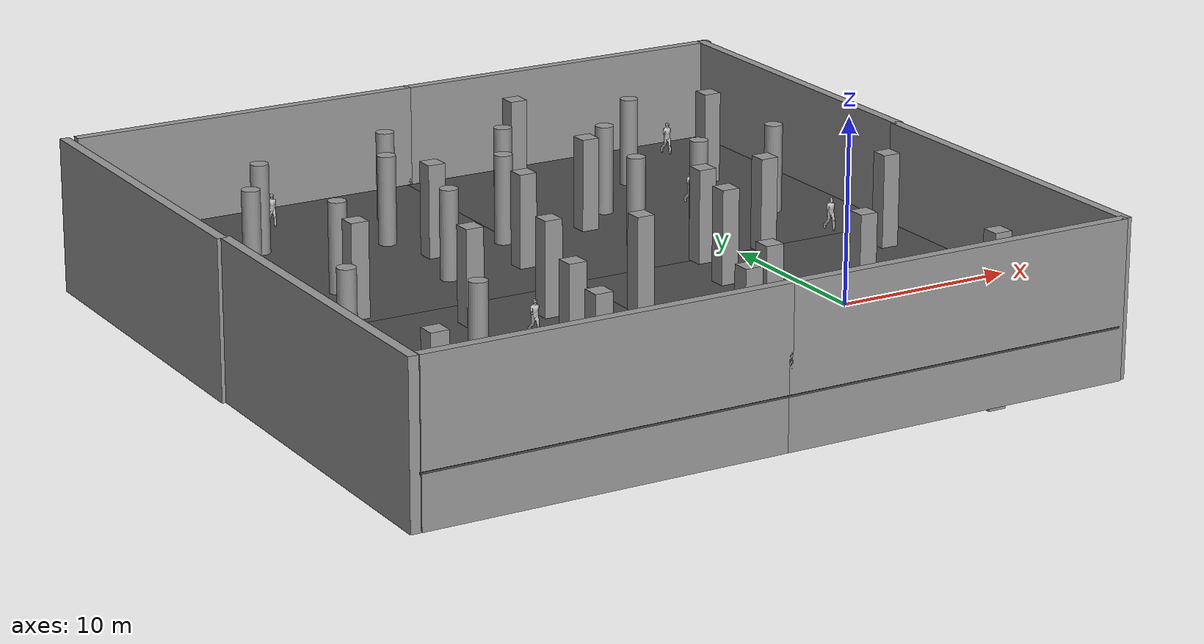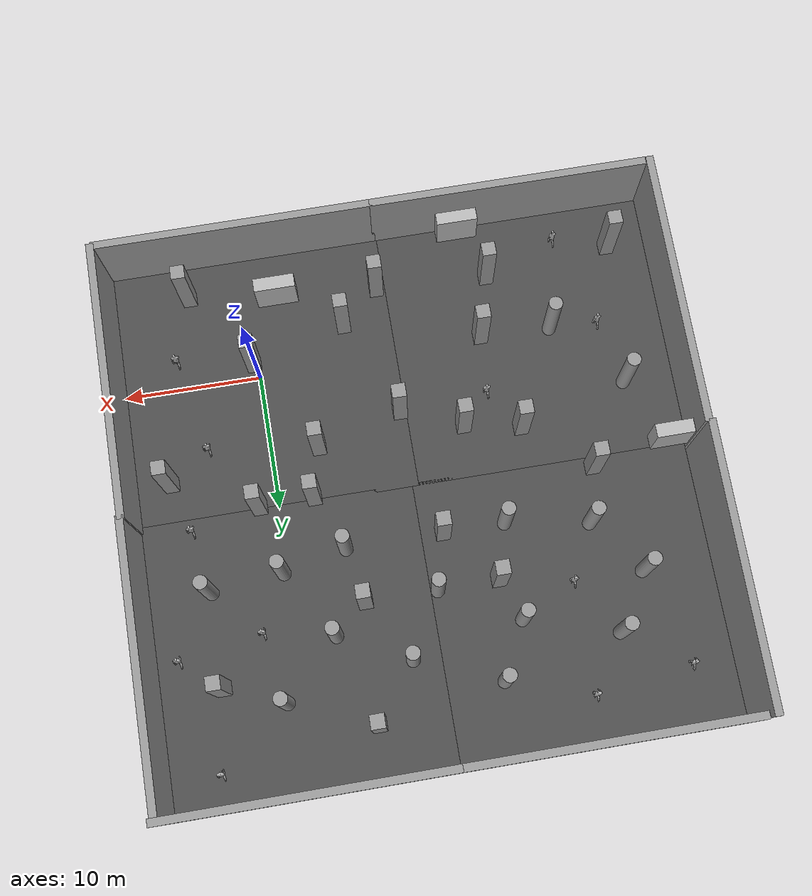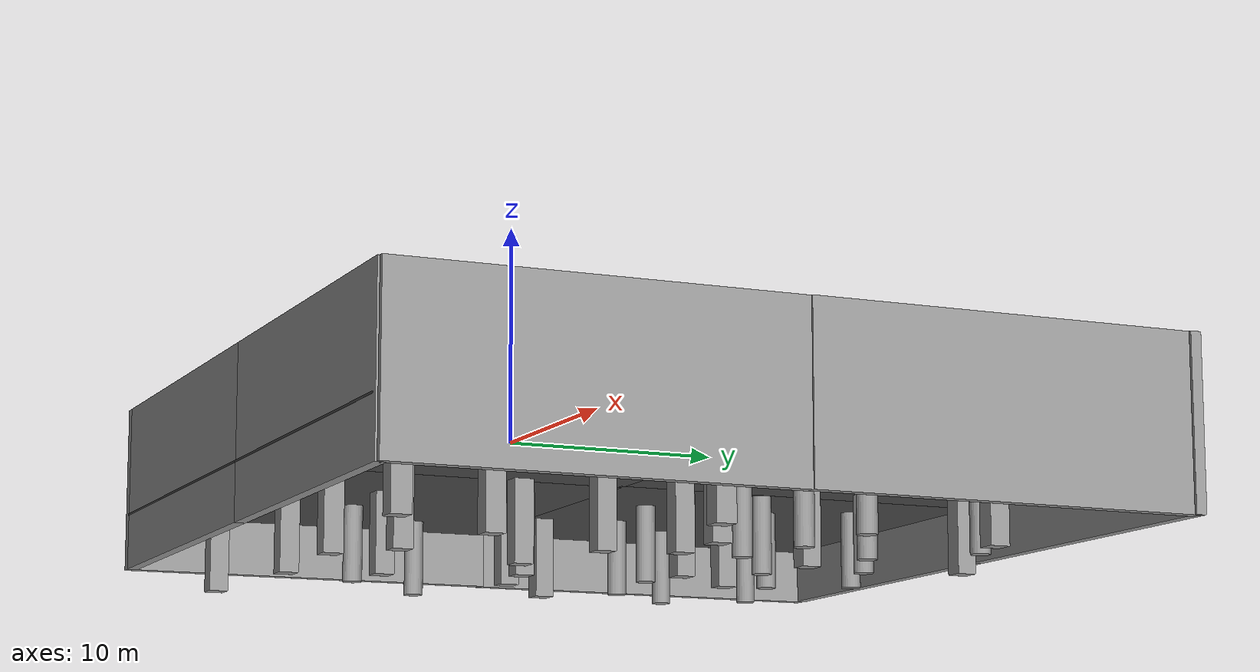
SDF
<?xml version='1.0'?>
<sdf version='1.6'>
  <model name='MW_world_1_0'>
    <link name='link_0'>
      <pose frame=''>-18.1125 7.0006 0.5 0 -0 0</pose>
      <inertial>
        <mass>9.47467</mass>
        <inertia>
          <ixx>71.6676</ixx>
          <ixy>0</ixy>
          <ixz>0</ixz>
          <iyy>71.6676</iyy>
          <iyz>0</iyz>
          <izz>1.57911</izz>
        </inertia>
        <pose frame=''>0 0 0 0 -0 0</pose>
      </inertial>
      <self_collide>0</self_collide>
      <kinematic>0</kinematic>
      <visual name='visual'>
        <pose frame=''>0 0 0 0 -0 0</pose>
        <geometry>
          <box>
            <size>1 1 9.47467</size>
          </box>
        </geometry>
        <material>
          <lighting>1</lighting>
          <script>
            <uri>file://media/materials/scripts/gazebo.material</uri>
            <name>Gazebo/Grey</name>
          </script>
          <ambient>0.3 0.3 0.3 1</ambient>
          <diffuse>0.7 0.7 0.7 1</diffuse>
          <specular>0.01 0.01 0.01 1</specular>
          <emissive>0 0 0 1</emissive>
        </material>
        <cast_shadows>1</cast_shadows>
        <transparency>0</transparency>
      </visual>
      <collision name='collision'>
        <laser_retro>0</laser_retro>
        <max_contacts>10</max_contacts>
        <pose frame=''>0 0 0 0 -0 0</pose>
        <geometry>
          <box>
            <size>1 1 9.47467</size>
          </box>
        </geometry>
        <surface>
          <friction>
            <ode>
              <mu>1</mu>
              <mu2>1</mu2>
              <fdir1>0 0 0</fdir1>
              <slip1>0</slip1>
              <slip2>0</slip2>
            </ode>
            <torsional>
              <coefficient>1</coefficient>
              <patch_radius>0</patch_radius>
              <surface_radius>0</surface_radius>
              <use_patch_radius>1</use_patch_radius>
              <ode>
                <slip>0</slip>
              </ode>
            </torsional>
          </friction>
          <bounce>
            <restitution_coefficient>0</restitution_coefficient>
            <threshold>1e+06</threshold>
          </bounce>
          <contact>
            <collide_without_contact>0</collide_without_contact>
            <collide_without_contact_bitmask>1</collide_without_contact_bitmask>
            <collide_bitmask>1</collide_bitmask>
            <ode>
              <soft_cfm>0</soft_cfm>
              <soft_erp>0.2</soft_erp>
              <kp>1e+13</kp>
              <kd>1</kd>
              <max_vel>0.01</max_vel>
              <min_depth>0</min_depth>
            </ode>
            <bullet>
              <split_impulse>1</split_impulse>
              <split_impulse_penetration_threshold>-0.01</split_impulse_penetration_threshold>
              <soft_cfm>0</soft_cfm>
              <soft_erp>0.2</soft_erp>
              <kp>1e+13</kp>
              <kd>1</kd>
            </bullet>
          </contact>
        </surface>
      </collision>
    </link>
    <link name='link_0_0'>
      <pose frame=''>-21.6457 14.7871 0.5 0 -0 0</pose>
      <inertial>
        <mass>9.05819</mass>
        <inertia>
          <ixx>62.5018</ixx>
          <ixy>0</ixy>
          <ixz>0</ixz>
          <iyy>62.5018</iyy>
          <iyz>0</iyz>
          <izz>1.13227</izz>
        </inertia>
        <pose frame=''>0 0 0 0 -0 0</pose>
      </inertial>
      <self_collide>0</self_collide>
      <kinematic>0</kinematic>
      <visual name='visual'>
        <pose frame=''>0 0 0 0 -0 0</pose>
        <geometry>
          <cylinder>
            <radius>0.5</radius>
            <length>9.05819</length>
          </cylinder>
        </geometry>
        <material>
          <lighting>1</lighting>
          <script>
            <uri>file://media/materials/scripts/gazebo.material</uri>
            <name>Gazebo/Grey</name>
          </script>
          <ambient>0.3 0.3 0.3 1</ambient>
          <diffuse>0.7 0.7 0.7 1</diffuse>
          <specular>0.01 0.01 0.01 1</specular>
          <emissive>0 0 0 1</emissive>
        </material>
        <cast_shadows>1</cast_shadows>
        <transparency>0</transparency>
      </visual>
      <collision name='collision'>
        <laser_retro>0</laser_retro>
        <max_contacts>10</max_contacts>
        <pose frame=''>0 0 0 0 -0 0</pose>
        <geometry>
          <cylinder>
            <radius>0.5</radius>
            <length>9.05819</length>
          </cylinder>
        </geometry>
        <surface>
          <friction>
            <ode>
              <mu>1</mu>
              <mu2>1</mu2>
              <fdir1>0 0 0</fdir1>
              <slip1>0</slip1>
              <slip2>0</slip2>
            </ode>
            <torsional>
              <coefficient>1</coefficient>
              <patch_radius>0</patch_radius>
              <surface_radius>0</surface_radius>
              <use_patch_radius>1</use_patch_radius>
              <ode>
                <slip>0</slip>
              </ode>
            </torsional>
          </friction>
          <bounce>
            <restitution_coefficient>0</restitution_coefficient>
            <threshold>1e+06</threshold>
          </bounce>
          <contact>
            <collide_without_contact>0</collide_without_contact>
            <collide_without_contact_bitmask>1</collide_without_contact_bitmask>
            <collide_bitmask>1</collide_bitmask>
            <ode>
              <soft_cfm>0</soft_cfm>
              <soft_erp>0.2</soft_erp>
              <kp>1e+13</kp>
              <kd>1</kd>
              <max_vel>0.01</max_vel>
              <min_depth>0</min_depth>
            </ode>
            <bullet>
              <split_impulse>1</split_impulse>
              <split_impulse_penetration_threshold>-0.01</split_impulse_penetration_threshold>
              <soft_cfm>0</soft_cfm>
              <soft_erp>0.2</soft_erp>
              <kp>1e+13</kp>
              <kd>1</kd>
            </bullet>
          </contact>
        </surface>
      </collision>
    </link>
    <link name='link_0_0_clone'>
      <pose frame=''>-13.6457 24.7871 0.5 0 -0 0</pose>
      <inertial>
        <mass>9.05819</mass>
        <inertia>
          <ixx>62.5018</ixx>
          <ixy>0</ixy>
          <ixz>0</ixz>
          <iyy>62.5018</iyy>
          <iyz>0</iyz>
          <izz>1.13227</izz>
        </inertia>
        <pose frame=''>0 0 0 0 -0 0</pose>
      </inertial>
      <self_collide>0</self_collide>
      <kinematic>0</kinematic>
      <visual name='visual_0'>
        <pose frame=''>0 0 0 0 -0 0</pose>
        <geometry>
          <cylinder>
            <radius>0.5</radius>
            <length>9.05819</length>
          </cylinder>
        </geometry>
        <material>
          <lighting>1</lighting>
          <script>
            <uri>file://media/materials/scripts/gazebo.material</uri>
            <name>Gazebo/Grey</name>
          </script>
          <ambient>0.3 0.3 0.3 1</ambient>
          <diffuse>0.7 0.7 0.7 1</diffuse>
          <specular>0.01 0.01 0.01 1</specular>
          <emissive>0 0 0 1</emissive>
          <shader type='pixel'/>
        </material>
        <cast_shadows>1</cast_shadows>
        <transparency>0</transparency>
      </visual>
      <collision name='collision'>
        <laser_retro>0</laser_retro>
        <max_contacts>10</max_contacts>
        <pose frame=''>0 0 0 0 -0 0</pose>
        <geometry>
          <cylinder>
            <radius>0.5</radius>
            <length>9.05819</length>
          </cylinder>
        </geometry>
        <surface>
          <friction>
            <ode>
              <mu>1</mu>
              <mu2>1</mu2>
              <fdir1>0 0 0</fdir1>
              <slip1>0</slip1>
              <slip2>0</slip2>
            </ode>
            <torsional>
              <coefficient>1</coefficient>
              <patch_radius>0</patch_radius>
              <surface_radius>0</surface_radius>
              <use_patch_radius>1</use_patch_radius>
              <ode>
                <slip>0</slip>
              </ode>
            </torsional>
          </friction>
          <bounce>
            <restitution_coefficient>0</restitution_coefficient>
            <threshold>1e+06</threshold>
          </bounce>
          <contact>
            <collide_without_contact>0</collide_without_contact>
            <collide_without_contact_bitmask>1</collide_without_contact_bitmask>
            <collide_bitmask>1</collide_bitmask>
            <ode>
              <soft_cfm>0</soft_cfm>
              <soft_erp>0.2</soft_erp>
              <kp>1e+13</kp>
              <kd>1</kd>
              <max_vel>0.01</max_vel>
              <min_depth>0</min_depth>
            </ode>
            <bullet>
              <split_impulse>1</split_impulse>
              <split_impulse_penetration_threshold>-0.01</split_impulse_penetration_threshold>
              <soft_cfm>0</soft_cfm>
              <soft_erp>0.2</soft_erp>
              <kp>1e+13</kp>
              <kd>1</kd>
            </bullet>
          </contact>
        </surface>
      </collision>
    </link>
    <link name='link_0_0_clone_0'>
      <pose frame=''>0.35425 14.7871 0.5 0 -0 0</pose>
      <inertial>
        <mass>9.05819</mass>
        <inertia>
          <ixx>62.5018</ixx>
          <ixy>0</ixy>
          <ixz>0</ixz>
          <iyy>62.5018</iyy>
          <iyz>0</iyz>
          <izz>1.13227</izz>
        </inertia>
        <pose frame=''>0 0 0 0 -0 0</pose>
      </inertial>
      <self_collide>0</self_collide>
      <kinematic>0</kinematic>
      <visual name='visual_0'>
        <pose frame=''>0 0 0 0 -0 0</pose>
        <geometry>
          <cylinder>
            <radius>0.5</radius>
            <length>9.05819</length>
          </cylinder>
        </geometry>
        <material>
          <lighting>1</lighting>
          <script>
            <uri>file://media/materials/scripts/gazebo.material</uri>
            <name>Gazebo/Grey</name>
          </script>
          <ambient>0.3 0.3 0.3 1</ambient>
          <diffuse>0.7 0.7 0.7 1</diffuse>
          <specular>0.01 0.01 0.01 1</specular>
          <emissive>0 0 0 1</emissive>
          <shader type='pixel'/>
        </material>
        <cast_shadows>1</cast_shadows>
        <transparency>0</transparency>
      </visual>
      <collision name='collision'>
        <laser_retro>0</laser_retro>
        <max_contacts>10</max_contacts>
        <pose frame=''>0 0 0 0 -0 0</pose>
        <geometry>
          <cylinder>
            <radius>0.5</radius>
            <length>9.05819</length>
          </cylinder>
        </geometry>
        <surface>
          <friction>
            <ode>
              <mu>1</mu>
              <mu2>1</mu2>
              <fdir1>0 0 0</fdir1>
              <slip1>0</slip1>
              <slip2>0</slip2>
            </ode>
            <torsional>
              <coefficient>1</coefficient>
              <patch_radius>0</patch_radius>
              <surface_radius>0</surface_radius>
              <use_patch_radius>1</use_patch_radius>
              <ode>
                <slip>0</slip>
              </ode>
            </torsional>
          </friction>
          <bounce>
            <restitution_coefficient>0</restitution_coefficient>
            <threshold>1e+06</threshold>
          </bounce>
          <contact>
            <collide_without_contact>0</collide_without_contact>
            <collide_without_contact_bitmask>1</collide_without_contact_bitmask>
            <collide_bitmask>1</collide_bitmask>
            <ode>
              <soft_cfm>0</soft_cfm>
              <soft_erp>0.2</soft_erp>
              <kp>1e+13</kp>
              <kd>1</kd>
              <max_vel>0.01</max_vel>
              <min_depth>0</min_depth>
            </ode>
            <bullet>
              <split_impulse>1</split_impulse>
              <split_impulse_penetration_threshold>-0.01</split_impulse_penetration_threshold>
              <soft_cfm>0</soft_cfm>
              <soft_erp>0.2</soft_erp>
              <kp>1e+13</kp>
              <kd>1</kd>
            </bullet>
          </contact>
        </surface>
      </collision>
    </link>
    <link name='link_0_0_clone_1'>
      <pose frame=''>1.35425 23.7871 0.5 0 -0 0</pose>
      <inertial>
        <mass>9.05819</mass>
        <inertia>
          <ixx>62.5018</ixx>
          <ixy>0</ixy>
          <ixz>0</ixz>
          <iyy>62.5018</iyy>
          <iyz>0</iyz>
          <izz>1.13227</izz>
        </inertia>
        <pose frame=''>0 0 0 0 -0 0</pose>
      </inertial>
      <self_collide>0</self_collide>
      <kinematic>0</kinematic>
      <visual name='visual_0'>
        <pose frame=''>0 0 0 0 -0 0</pose>
        <geometry>
          <cylinder>
            <radius>0.5</radius>
            <length>9.05819</length>
          </cylinder>
        </geometry>
        <material>
          <lighting>1</lighting>
          <script>
            <uri>file://media/materials/scripts/gazebo.material</uri>
            <name>Gazebo/Grey</name>
          </script>
          <ambient>0.3 0.3 0.3 1</ambient>
          <diffuse>0.7 0.7 0.7 1</diffuse>
          <specular>0.01 0.01 0.01 1</specular>
          <emissive>0 0 0 1</emissive>
          <shader type='pixel'/>
        </material>
        <cast_shadows>1</cast_shadows>
        <transparency>0</transparency>
      </visual>
      <collision name='collision'>
        <laser_retro>0</laser_retro>
        <max_contacts>10</max_contacts>
        <pose frame=''>0 0 0 0 -0 0</pose>
        <geometry>
          <cylinder>
            <radius>0.5</radius>
            <length>9.05819</length>
          </cylinder>
        </geometry>
        <surface>
          <friction>
            <ode>
              <mu>1</mu>
              <mu2>1</mu2>
              <fdir1>0 0 0</fdir1>
              <slip1>0</slip1>
              <slip2>0</slip2>
            </ode>
            <torsional>
              <coefficient>1</coefficient>
              <patch_radius>0</patch_radius>
              <surface_radius>0</surface_radius>
              <use_patch_radius>1</use_patch_radius>
              <ode>
                <slip>0</slip>
              </ode>
            </torsional>
          </friction>
          <bounce>
            <restitution_coefficient>0</restitution_coefficient>
            <threshold>1e+06</threshold>
          </bounce>
          <contact>
            <collide_without_contact>0</collide_without_contact>
            <collide_without_contact_bitmask>1</collide_without_contact_bitmask>
            <collide_bitmask>1</collide_bitmask>
            <ode>
              <soft_cfm>0</soft_cfm>
              <soft_erp>0.2</soft_erp>
              <kp>1e+13</kp>
              <kd>1</kd>
              <max_vel>0.01</max_vel>
              <min_depth>0</min_depth>
            </ode>
            <bullet>
              <split_impulse>1</split_impulse>
              <split_impulse_penetration_threshold>-0.01</split_impulse_penetration_threshold>
              <soft_cfm>0</soft_cfm>
              <soft_erp>0.2</soft_erp>
              <kp>1e+13</kp>
              <kd>1</kd>
            </bullet>
          </contact>
        </surface>
      </collision>
    </link>
    <link name='link_0_0_clone_10'>
      <pose frame=''>5.5552 15.3295 0.5 0 -0 0</pose>
      <inertial>
        <mass>9.05819</mass>
        <inertia>
          <ixx>62.5018</ixx>
          <ixy>0</ixy>
          <ixz>0</ixz>
          <iyy>62.5018</iyy>
          <iyz>0</iyz>
          <izz>1.13227</izz>
        </inertia>
        <pose frame=''>0 0 0 0 -0 0</pose>
      </inertial>
      <self_collide>0</self_collide>
      <kinematic>0</kinematic>
      <visual name='visual_0'>
        <pose frame=''>0 0 0 0 -0 0</pose>
        <geometry>
          <cylinder>
            <radius>0.5</radius>
            <length>9.05819</length>
          </cylinder>
        </geometry>
        <material>
          <lighting>1</lighting>
          <script>
            <uri>file://media/materials/scripts/gazebo.material</uri>
            <name>Gazebo/Grey</name>
          </script>
          <ambient>0.3 0.3 0.3 1</ambient>
          <diffuse>0.7 0.7 0.7 1</diffuse>
          <specular>0.01 0.01 0.01 1</specular>
          <emissive>0 0 0 1</emissive>
          <shader type='pixel'/>
        </material>
        <cast_shadows>1</cast_shadows>
        <transparency>0</transparency>
      </visual>
      <collision name='collision'>
        <laser_retro>0</laser_retro>
        <max_contacts>10</max_contacts>
        <pose frame=''>0 0 0 0 -0 0</pose>
        <geometry>
          <cylinder>
            <radius>0.5</radius>
            <length>9.05819</length>
          </cylinder>
        </geometry>
        <surface>
          <friction>
            <ode>
              <mu>1</mu>
              <mu2>1</mu2>
              <fdir1>0 0 0</fdir1>
              <slip1>0</slip1>
              <slip2>0</slip2>
            </ode>
            <torsional>
              <coefficient>1</coefficient>
              <patch_radius>0</patch_radius>
              <surface_radius>0</surface_radius>
              <use_patch_radius>1</use_patch_radius>
              <ode>
                <slip>0</slip>
              </ode>
            </torsional>
          </friction>
          <bounce>
            <restitution_coefficient>0</restitution_coefficient>
            <threshold>1e+06</threshold>
          </bounce>
          <contact>
            <collide_without_contact>0</collide_without_contact>
            <collide_without_contact_bitmask>1</collide_without_contact_bitmask>
            <collide_bitmask>1</collide_bitmask>
            <ode>
              <soft_cfm>0</soft_cfm>
              <soft_erp>0.2</soft_erp>
              <kp>1e+13</kp>
              <kd>1</kd>
              <max_vel>0.01</max_vel>
              <min_depth>0</min_depth>
            </ode>
            <bullet>
              <split_impulse>1</split_impulse>
              <split_impulse_penetration_threshold>-0.01</split_impulse_penetration_threshold>
              <soft_cfm>0</soft_cfm>
              <soft_erp>0.2</soft_erp>
              <kp>1e+13</kp>
              <kd>1</kd>
            </bullet>
          </contact>
        </surface>
      </collision>
    </link>
    <link name='link_0_0_clone_11'>
      <pose frame=''>-21.6457 -0.212927 0.5 0 -0 0</pose>
      <inertial>
        <mass>9.05819</mass>
        <inertia>
          <ixx>62.5018</ixx>
          <ixy>0</ixy>
          <ixz>0</ixz>
          <iyy>62.5018</iyy>
          <iyz>0</iyz>
          <izz>1.13227</izz>
        </inertia>
        <pose frame=''>0 0 0 0 -0 0</pose>
      </inertial>
      <self_collide>0</self_collide>
      <kinematic>0</kinematic>
      <visual name='visual_0'>
        <pose frame=''>0 0 0 0 -0 0</pose>
        <geometry>
          <cylinder>
            <radius>0.5</radius>
            <length>9.05819</length>
          </cylinder>
        </geometry>
        <material>
          <lighting>1</lighting>
          <script>
            <uri>file://media/materials/scripts/gazebo.material</uri>
            <name>Gazebo/Grey</name>
          </script>
          <ambient>0.3 0.3 0.3 1</ambient>
          <diffuse>0.7 0.7 0.7 1</diffuse>
          <specular>0.01 0.01 0.01 1</specular>
          <emissive>0 0 0 1</emissive>
          <shader type='pixel'/>
        </material>
        <cast_shadows>1</cast_shadows>
        <transparency>0</transparency>
      </visual>
      <collision name='collision'>
        <laser_retro>0</laser_retro>
        <max_contacts>10</max_contacts>
        <pose frame=''>0 0 0 0 -0 0</pose>
        <geometry>
          <cylinder>
            <radius>0.5</radius>
            <length>9.05819</length>
          </cylinder>
        </geometry>
        <surface>
          <friction>
            <ode>
              <mu>1</mu>
              <mu2>1</mu2>
              <fdir1>0 0 0</fdir1>
              <slip1>0</slip1>
              <slip2>0</slip2>
            </ode>
            <torsional>
              <coefficient>1</coefficient>
              <patch_radius>0</patch_radius>
              <surface_radius>0</surface_radius>
              <use_patch_radius>1</use_patch_radius>
              <ode>
                <slip>0</slip>
              </ode>
            </torsional>
          </friction>
          <bounce>
            <restitution_coefficient>0</restitution_coefficient>
            <threshold>1e+06</threshold>
          </bounce>
          <contact>
            <collide_without_contact>0</collide_without_contact>
            <collide_without_contact_bitmask>1</collide_without_contact_bitmask>
            <collide_bitmask>1</collide_bitmask>
            <ode>
              <soft_cfm>0</soft_cfm>
              <soft_erp>0.2</soft_erp>
              <kp>1e+13</kp>
              <kd>1</kd>
              <max_vel>0.01</max_vel>
              <min_depth>0</min_depth>
            </ode>
            <bullet>
              <split_impulse>1</split_impulse>
              <split_impulse_penetration_threshold>-0.01</split_impulse_penetration_threshold>
              <soft_cfm>0</soft_cfm>
              <soft_erp>0.2</soft_erp>
              <kp>1e+13</kp>
              <kd>1</kd>
            </bullet>
          </contact>
        </surface>
      </collision>
    </link>
    <link name='link_0_0_clone_12'>
      <pose frame=''>-26.2128 4.78707 0.5 0 -0 0</pose>
      <inertial>
        <mass>9.05819</mass>
        <inertia>
          <ixx>62.5018</ixx>
          <ixy>0</ixy>
          <ixz>0</ixz>
          <iyy>62.5018</iyy>
          <iyz>0</iyz>
          <izz>1.13227</izz>
        </inertia>
        <pose frame=''>0 0 0 0 -0 0</pose>
      </inertial>
      <self_collide>0</self_collide>
      <kinematic>0</kinematic>
      <visual name='visual_0'>
        <pose frame=''>0 0 0 0 -0 0</pose>
        <geometry>
          <cylinder>
            <radius>0.5</radius>
            <length>9.05819</length>
          </cylinder>
        </geometry>
        <material>
          <lighting>1</lighting>
          <script>
            <uri>file://media/materials/scripts/gazebo.material</uri>
            <name>Gazebo/Grey</name>
          </script>
          <ambient>0.3 0.3 0.3 1</ambient>
          <diffuse>0.7 0.7 0.7 1</diffuse>
          <specular>0.01 0.01 0.01 1</specular>
          <emissive>0 0 0 1</emissive>
          <shader type='pixel'/>
        </material>
        <cast_shadows>1</cast_shadows>
        <transparency>0</transparency>
      </visual>
      <collision name='collision'>
        <laser_retro>0</laser_retro>
        <max_contacts>10</max_contacts>
        <pose frame=''>0 0 0 0 -0 0</pose>
        <geometry>
          <cylinder>
            <radius>0.5</radius>
            <length>9.05819</length>
          </cylinder>
        </geometry>
        <surface>
          <friction>
            <ode>
              <mu>1</mu>
              <mu2>1</mu2>
              <fdir1>0 0 0</fdir1>
              <slip1>0</slip1>
              <slip2>0</slip2>
            </ode>
            <torsional>
              <coefficient>1</coefficient>
              <patch_radius>0</patch_radius>
              <surface_radius>0</surface_radius>
              <use_patch_radius>1</use_patch_radius>
              <ode>
                <slip>0</slip>
              </ode>
            </torsional>
          </friction>
          <bounce>
            <restitution_coefficient>0</restitution_coefficient>
            <threshold>1e+06</threshold>
          </bounce>
          <contact>
            <collide_without_contact>0</collide_without_contact>
            <collide_without_contact_bitmask>1</collide_without_contact_bitmask>
            <collide_bitmask>1</collide_bitmask>
            <ode>
              <soft_cfm>0</soft_cfm>
              <soft_erp>0.2</soft_erp>
              <kp>1e+13</kp>
              <kd>1</kd>
              <max_vel>0.01</max_vel>
              <min_depth>0</min_depth>
            </ode>
            <bullet>
              <split_impulse>1</split_impulse>
              <split_impulse_penetration_threshold>-0.01</split_impulse_penetration_threshold>
              <soft_cfm>0</soft_cfm>
              <soft_erp>0.2</soft_erp>
              <kp>1e+13</kp>
              <kd>1</kd>
            </bullet>
          </contact>
        </surface>
      </collision>
    </link>
    <link name='link_0_0_clone_2'>
      <pose frame=''>-10.147 17.7871 0.5 0 -0 0</pose>
      <inertial>
        <mass>9.05819</mass>
        <inertia>
          <ixx>62.5018</ixx>
          <ixy>0</ixy>
          <ixz>0</ixz>
          <iyy>62.5018</iyy>
          <iyz>0</iyz>
          <izz>1.13227</izz>
        </inertia>
        <pose frame=''>0 0 0 0 -0 0</pose>
      </inertial>
      <self_collide>0</self_collide>
      <kinematic>0</kinematic>
      <visual name='visual_0'>
        <pose frame=''>0 0 0 0 -0 0</pose>
        <geometry>
          <cylinder>
            <radius>0.5</radius>
            <length>9.05819</length>
          </cylinder>
        </geometry>
        <material>
          <lighting>1</lighting>
          <script>
            <uri>file://media/materials/scripts/gazebo.material</uri>
            <name>Gazebo/Grey</name>
          </script>
          <ambient>0.3 0.3 0.3 1</ambient>
          <diffuse>0.7 0.7 0.7 1</diffuse>
          <specular>0.01 0.01 0.01 1</specular>
          <emissive>0 0 0 1</emissive>
          <shader type='pixel'/>
        </material>
        <cast_shadows>1</cast_shadows>
        <transparency>0</transparency>
      </visual>
      <collision name='collision'>
        <laser_retro>0</laser_retro>
        <max_contacts>10</max_contacts>
        <pose frame=''>0 0 0 0 -0 0</pose>
        <geometry>
          <cylinder>
            <radius>0.5</radius>
            <length>9.05819</length>
          </cylinder>
        </geometry>
        <surface>
          <friction>
            <ode>
              <mu>1</mu>
              <mu2>1</mu2>
              <fdir1>0 0 0</fdir1>
              <slip1>0</slip1>
              <slip2>0</slip2>
            </ode>
            <torsional>
              <coefficient>1</coefficient>
              <patch_radius>0</patch_radius>
              <surface_radius>0</surface_radius>
              <use_patch_radius>1</use_patch_radius>
              <ode>
                <slip>0</slip>
              </ode>
            </torsional>
          </friction>
          <bounce>
            <restitution_coefficient>0</restitution_coefficient>
            <threshold>1e+06</threshold>
          </bounce>
          <contact>
            <collide_without_contact>0</collide_without_contact>
            <collide_without_contact_bitmask>1</collide_without_contact_bitmask>
            <collide_bitmask>1</collide_bitmask>
            <ode>
              <soft_cfm>0</soft_cfm>
              <soft_erp>0.2</soft_erp>
              <kp>1e+13</kp>
              <kd>1</kd>
              <max_vel>0.01</max_vel>
              <min_depth>0</min_depth>
            </ode>
            <bullet>
              <split_impulse>1</split_impulse>
              <split_impulse_penetration_threshold>-0.01</split_impulse_penetration_threshold>
              <soft_cfm>0</soft_cfm>
              <soft_erp>0.2</soft_erp>
              <kp>1e+13</kp>
              <kd>1</kd>
            </bullet>
          </contact>
        </surface>
      </collision>
    </link>
    <link name='link_0_0_clone_3'>
      <pose frame=''>-7.64575 22.3014 0.5 0 -0 0</pose>
      <inertial>
        <mass>9.05819</mass>
        <inertia>
          <ixx>62.5018</ixx>
          <ixy>0</ixy>
          <ixz>0</ixz>
          <iyy>62.5018</iyy>
          <iyz>0</iyz>
          <izz>1.13227</izz>
        </inertia>
        <pose frame=''>0 0 0 0 -0 0</pose>
      </inertial>
      <self_collide>0</self_collide>
      <kinematic>0</kinematic>
      <visual name='visual_0'>
        <pose frame=''>0 0 0 0 -0 0</pose>
        <geometry>
          <cylinder>
            <radius>0.5</radius>
            <length>9.05819</length>
          </cylinder>
        </geometry>
        <material>
          <lighting>1</lighting>
          <script>
            <uri>file://media/materials/scripts/gazebo.material</uri>
            <name>Gazebo/Grey</name>
          </script>
          <ambient>0.3 0.3 0.3 1</ambient>
          <diffuse>0.7 0.7 0.7 1</diffuse>
          <specular>0.01 0.01 0.01 1</specular>
          <emissive>0 0 0 1</emissive>
          <shader type='pixel'/>
        </material>
        <cast_shadows>1</cast_shadows>
        <transparency>0</transparency>
      </visual>
      <collision name='collision'>
        <laser_retro>0</laser_retro>
        <max_contacts>10</max_contacts>
        <pose frame=''>0 0 0 0 -0 0</pose>
        <geometry>
          <cylinder>
            <radius>0.5</radius>
            <length>9.05819</length>
          </cylinder>
        </geometry>
        <surface>
          <friction>
            <ode>
              <mu>1</mu>
              <mu2>1</mu2>
              <fdir1>0 0 0</fdir1>
              <slip1>0</slip1>
              <slip2>0</slip2>
            </ode>
            <torsional>
              <coefficient>1</coefficient>
              <patch_radius>0</patch_radius>
              <surface_radius>0</surface_radius>
              <use_patch_radius>1</use_patch_radius>
              <ode>
                <slip>0</slip>
              </ode>
            </torsional>
          </friction>
          <bounce>
            <restitution_coefficient>0</restitution_coefficient>
            <threshold>1e+06</threshold>
          </bounce>
          <contact>
            <collide_without_contact>0</collide_without_contact>
            <collide_without_contact_bitmask>1</collide_without_contact_bitmask>
            <collide_bitmask>1</collide_bitmask>
            <ode>
              <soft_cfm>0</soft_cfm>
              <soft_erp>0.2</soft_erp>
              <kp>1e+13</kp>
              <kd>1</kd>
              <max_vel>0.01</max_vel>
              <min_depth>0</min_depth>
            </ode>
            <bullet>
              <split_impulse>1</split_impulse>
              <split_impulse_penetration_threshold>-0.01</split_impulse_penetration_threshold>
              <soft_cfm>0</soft_cfm>
              <soft_erp>0.2</soft_erp>
              <kp>1e+13</kp>
              <kd>1</kd>
            </bullet>
          </contact>
        </surface>
      </collision>
    </link>
    <link name='link_0_0_clone_4'>
      <pose frame=''>-15.6457 20.7871 0.5 0 -0 0</pose>
      <inertial>
        <mass>9.05819</mass>
        <inertia>
          <ixx>62.5018</ixx>
          <ixy>0</ixy>
          <ixz>0</ixz>
          <iyy>62.5018</iyy>
          <iyz>0</iyz>
          <izz>1.13227</izz>
        </inertia>
        <pose frame=''>0 0 0 0 -0 0</pose>
      </inertial>
      <self_collide>0</self_collide>
      <kinematic>0</kinematic>
      <visual name='visual_0'>
        <pose frame=''>0 0 0 0 -0 0</pose>
        <geometry>
          <cylinder>
            <radius>0.5</radius>
            <length>9.05819</length>
          </cylinder>
        </geometry>
        <material>
          <lighting>1</lighting>
          <script>
            <uri>file://media/materials/scripts/gazebo.material</uri>
            <name>Gazebo/Grey</name>
          </script>
          <ambient>0.3 0.3 0.3 1</ambient>
          <diffuse>0.7 0.7 0.7 1</diffuse>
          <specular>0.01 0.01 0.01 1</specular>
          <emissive>0 0 0 1</emissive>
          <shader type='pixel'/>
        </material>
        <cast_shadows>1</cast_shadows>
        <transparency>0</transparency>
      </visual>
      <collision name='collision'>
        <laser_retro>0</laser_retro>
        <max_contacts>10</max_contacts>
        <pose frame=''>0 0 0 0 -0 0</pose>
        <geometry>
          <cylinder>
            <radius>0.5</radius>
            <length>9.05819</length>
          </cylinder>
        </geometry>
        <surface>
          <friction>
            <ode>
              <mu>1</mu>
              <mu2>1</mu2>
              <fdir1>0 0 0</fdir1>
              <slip1>0</slip1>
              <slip2>0</slip2>
            </ode>
            <torsional>
              <coefficient>1</coefficient>
              <patch_radius>0</patch_radius>
              <surface_radius>0</surface_radius>
              <use_patch_radius>1</use_patch_radius>
              <ode>
                <slip>0</slip>
              </ode>
            </torsional>
          </friction>
          <bounce>
            <restitution_coefficient>0</restitution_coefficient>
            <threshold>1e+06</threshold>
          </bounce>
          <contact>
            <collide_without_contact>0</collide_without_contact>
            <collide_without_contact_bitmask>1</collide_without_contact_bitmask>
            <collide_bitmask>1</collide_bitmask>
            <ode>
              <soft_cfm>0</soft_cfm>
              <soft_erp>0.2</soft_erp>
              <kp>1e+13</kp>
              <kd>1</kd>
              <max_vel>0.01</max_vel>
              <min_depth>0</min_depth>
            </ode>
            <bullet>
              <split_impulse>1</split_impulse>
              <split_impulse_penetration_threshold>-0.01</split_impulse_penetration_threshold>
              <soft_cfm>0</soft_cfm>
              <soft_erp>0.2</soft_erp>
              <kp>1e+13</kp>
              <kd>1</kd>
            </bullet>
          </contact>
        </surface>
      </collision>
    </link>
    <link name='link_0_0_clone_5'>
      <pose frame=''>-15.6457 13.7871 0.5 0 -0 0</pose>
      <inertial>
        <mass>9.05819</mass>
        <inertia>
          <ixx>62.5018</ixx>
          <ixy>0</ixy>
          <ixz>0</ixz>
          <iyy>62.5018</iyy>
          <iyz>0</iyz>
          <izz>1.13227</izz>
        </inertia>
        <pose frame=''>0 0 0 0 -0 0</pose>
      </inertial>
      <self_collide>0</self_collide>
      <kinematic>0</kinematic>
      <visual name='visual_0'>
        <pose frame=''>0 0 0 0 -0 0</pose>
        <geometry>
          <cylinder>
            <radius>0.5</radius>
            <length>9.05819</length>
          </cylinder>
        </geometry>
        <material>
          <lighting>1</lighting>
          <script>
            <uri>file://media/materials/scripts/gazebo.material</uri>
            <name>Gazebo/Grey</name>
          </script>
          <ambient>0.3 0.3 0.3 1</ambient>
          <diffuse>0.7 0.7 0.7 1</diffuse>
          <specular>0.01 0.01 0.01 1</specular>
          <emissive>0 0 0 1</emissive>
          <shader type='pixel'/>
        </material>
        <cast_shadows>1</cast_shadows>
        <transparency>0</transparency>
      </visual>
      <collision name='collision'>
        <laser_retro>0</laser_retro>
        <max_contacts>10</max_contacts>
        <pose frame=''>0 0 0 0 -0 0</pose>
        <geometry>
          <cylinder>
            <radius>0.5</radius>
            <length>9.05819</length>
          </cylinder>
        </geometry>
        <surface>
          <friction>
            <ode>
              <mu>1</mu>
              <mu2>1</mu2>
              <fdir1>0 0 0</fdir1>
              <slip1>0</slip1>
              <slip2>0</slip2>
            </ode>
            <torsional>
              <coefficient>1</coefficient>
              <patch_radius>0</patch_radius>
              <surface_radius>0</surface_radius>
              <use_patch_radius>1</use_patch_radius>
              <ode>
                <slip>0</slip>
              </ode>
            </torsional>
          </friction>
          <bounce>
            <restitution_coefficient>0</restitution_coefficient>
            <threshold>1e+06</threshold>
          </bounce>
          <contact>
            <collide_without_contact>0</collide_without_contact>
            <collide_without_contact_bitmask>1</collide_without_contact_bitmask>
            <collide_bitmask>1</collide_bitmask>
            <ode>
              <soft_cfm>0</soft_cfm>
              <soft_erp>0.2</soft_erp>
              <kp>1e+13</kp>
              <kd>1</kd>
              <max_vel>0.01</max_vel>
              <min_depth>0</min_depth>
            </ode>
            <bullet>
              <split_impulse>1</split_impulse>
              <split_impulse_penetration_threshold>-0.01</split_impulse_penetration_threshold>
              <soft_cfm>0</soft_cfm>
              <soft_erp>0.2</soft_erp>
              <kp>1e+13</kp>
              <kd>1</kd>
            </bullet>
          </contact>
        </surface>
      </collision>
    </link>
    <link name='link_0_0_clone_6'>
      <pose frame=''>-22.2188 22.7871 0.5 0 -0 0</pose>
      <inertial>
        <mass>9.05819</mass>
        <inertia>
          <ixx>62.5018</ixx>
          <ixy>0</ixy>
          <ixz>0</ixz>
          <iyy>62.5018</iyy>
          <iyz>0</iyz>
          <izz>1.13227</izz>
        </inertia>
        <pose frame=''>0 0 0 0 -0 0</pose>
      </inertial>
      <self_collide>0</self_collide>
      <kinematic>0</kinematic>
      <visual name='visual_0'>
        <pose frame=''>0 0 0 0 -0 0</pose>
        <geometry>
          <cylinder>
            <radius>0.5</radius>
            <length>9.05819</length>
          </cylinder>
        </geometry>
        <material>
          <lighting>1</lighting>
          <script>
            <uri>file://media/materials/scripts/gazebo.material</uri>
            <name>Gazebo/Grey</name>
          </script>
          <ambient>0.3 0.3 0.3 1</ambient>
          <diffuse>0.7 0.7 0.7 1</diffuse>
          <specular>0.01 0.01 0.01 1</specular>
          <emissive>0 0 0 1</emissive>
          <shader type='pixel'/>
        </material>
        <cast_shadows>1</cast_shadows>
        <transparency>0</transparency>
      </visual>
      <collision name='collision'>
        <laser_retro>0</laser_retro>
        <max_contacts>10</max_contacts>
        <pose frame=''>0 0 0 0 -0 0</pose>
        <geometry>
          <cylinder>
            <radius>0.5</radius>
            <length>9.05819</length>
          </cylinder>
        </geometry>
        <surface>
          <friction>
            <ode>
              <mu>1</mu>
              <mu2>1</mu2>
              <fdir1>0 0 0</fdir1>
              <slip1>0</slip1>
              <slip2>0</slip2>
            </ode>
            <torsional>
              <coefficient>1</coefficient>
              <patch_radius>0</patch_radius>
              <surface_radius>0</surface_radius>
              <use_patch_radius>1</use_patch_radius>
              <ode>
                <slip>0</slip>
              </ode>
            </torsional>
          </friction>
          <bounce>
            <restitution_coefficient>0</restitution_coefficient>
            <threshold>1e+06</threshold>
          </bounce>
          <contact>
            <collide_without_contact>0</collide_without_contact>
            <collide_without_contact_bitmask>1</collide_without_contact_bitmask>
            <collide_bitmask>1</collide_bitmask>
            <ode>
              <soft_cfm>0</soft_cfm>
              <soft_erp>0.2</soft_erp>
              <kp>1e+13</kp>
              <kd>1</kd>
              <max_vel>0.01</max_vel>
              <min_depth>0</min_depth>
            </ode>
            <bullet>
              <split_impulse>1</split_impulse>
              <split_impulse_penetration_threshold>-0.01</split_impulse_penetration_threshold>
              <soft_cfm>0</soft_cfm>
              <soft_erp>0.2</soft_erp>
              <kp>1e+13</kp>
              <kd>1</kd>
            </bullet>
          </contact>
        </surface>
      </collision>
    </link>
    <link name='link_0_0_clone_7'>
      <pose frame=''>-24.6457 18.7871 0.5 0 -0 0</pose>
      <inertial>
        <mass>9.05819</mass>
        <inertia>
          <ixx>62.5018</ixx>
          <ixy>0</ixy>
          <ixz>0</ixz>
          <iyy>62.5018</iyy>
          <iyz>0</iyz>
          <izz>1.13227</izz>
        </inertia>
        <pose frame=''>0 0 0 0 -0 0</pose>
      </inertial>
      <self_collide>0</self_collide>
      <kinematic>0</kinematic>
      <visual name='visual_0'>
        <pose frame=''>0 0 0 0 -0 0</pose>
        <geometry>
          <cylinder>
            <radius>0.5</radius>
            <length>9.05819</length>
          </cylinder>
        </geometry>
        <material>
          <lighting>1</lighting>
          <script>
            <uri>file://media/materials/scripts/gazebo.material</uri>
            <name>Gazebo/Grey</name>
          </script>
          <ambient>0.3 0.3 0.3 1</ambient>
          <diffuse>0.7 0.7 0.7 1</diffuse>
          <specular>0.01 0.01 0.01 1</specular>
          <emissive>0 0 0 1</emissive>
          <shader type='pixel'/>
        </material>
        <cast_shadows>1</cast_shadows>
        <transparency>0</transparency>
      </visual>
      <collision name='collision'>
        <laser_retro>0</laser_retro>
        <max_contacts>10</max_contacts>
        <pose frame=''>0 0 0 0 -0 0</pose>
        <geometry>
          <cylinder>
            <radius>0.5</radius>
            <length>9.05819</length>
          </cylinder>
        </geometry>
        <surface>
          <friction>
            <ode>
              <mu>1</mu>
              <mu2>1</mu2>
              <fdir1>0 0 0</fdir1>
              <slip1>0</slip1>
              <slip2>0</slip2>
            </ode>
            <torsional>
              <coefficient>1</coefficient>
              <patch_radius>0</patch_radius>
              <surface_radius>0</surface_radius>
              <use_patch_radius>1</use_patch_radius>
              <ode>
                <slip>0</slip>
              </ode>
            </torsional>
          </friction>
          <bounce>
            <restitution_coefficient>0</restitution_coefficient>
            <threshold>1e+06</threshold>
          </bounce>
          <contact>
            <collide_without_contact>0</collide_without_contact>
            <collide_without_contact_bitmask>1</collide_without_contact_bitmask>
            <collide_bitmask>1</collide_bitmask>
            <ode>
              <soft_cfm>0</soft_cfm>
              <soft_erp>0.2</soft_erp>
              <kp>1e+13</kp>
              <kd>1</kd>
              <max_vel>0.01</max_vel>
              <min_depth>0</min_depth>
            </ode>
            <bullet>
              <split_impulse>1</split_impulse>
              <split_impulse_penetration_threshold>-0.01</split_impulse_penetration_threshold>
              <soft_cfm>0</soft_cfm>
              <soft_erp>0.2</soft_erp>
              <kp>1e+13</kp>
              <kd>1</kd>
            </bullet>
          </contact>
        </surface>
      </collision>
    </link>
    <link name='link_0_0_clone_8'>
      <pose frame=''>-4.23431 13.7871 0.5 0 -0 0</pose>
      <inertial>
        <mass>9.05819</mass>
        <inertia>
          <ixx>62.5018</ixx>
          <ixy>0</ixy>
          <ixz>0</ixz>
          <iyy>62.5018</iyy>
          <iyz>0</iyz>
          <izz>1.13227</izz>
        </inertia>
        <pose frame=''>0 0 0 0 -0 0</pose>
      </inertial>
      <self_collide>0</self_collide>
      <kinematic>0</kinematic>
      <visual name='visual_0'>
        <pose frame=''>0 0 0 0 -0 0</pose>
        <geometry>
          <cylinder>
            <radius>0.5</radius>
            <length>9.05819</length>
          </cylinder>
        </geometry>
        <material>
          <lighting>1</lighting>
          <script>
            <uri>file://media/materials/scripts/gazebo.material</uri>
            <name>Gazebo/Grey</name>
          </script>
          <ambient>0.3 0.3 0.3 1</ambient>
          <diffuse>0.7 0.7 0.7 1</diffuse>
          <specular>0.01 0.01 0.01 1</specular>
          <emissive>0 0 0 1</emissive>
          <shader type='pixel'/>
        </material>
        <cast_shadows>1</cast_shadows>
        <transparency>0</transparency>
      </visual>
      <collision name='collision'>
        <laser_retro>0</laser_retro>
        <max_contacts>10</max_contacts>
        <pose frame=''>0 0 0 0 -0 0</pose>
        <geometry>
          <cylinder>
            <radius>0.5</radius>
            <length>9.05819</length>
          </cylinder>
        </geometry>
        <surface>
          <friction>
            <ode>
              <mu>1</mu>
              <mu2>1</mu2>
              <fdir1>0 0 0</fdir1>
              <slip1>0</slip1>
              <slip2>0</slip2>
            </ode>
            <torsional>
              <coefficient>1</coefficient>
              <patch_radius>0</patch_radius>
              <surface_radius>0</surface_radius>
              <use_patch_radius>1</use_patch_radius>
              <ode>
                <slip>0</slip>
              </ode>
            </torsional>
          </friction>
          <bounce>
            <restitution_coefficient>0</restitution_coefficient>
            <threshold>1e+06</threshold>
          </bounce>
          <contact>
            <collide_without_contact>0</collide_without_contact>
            <collide_without_contact_bitmask>1</collide_without_contact_bitmask>
            <collide_bitmask>1</collide_bitmask>
            <ode>
              <soft_cfm>0</soft_cfm>
              <soft_erp>0.2</soft_erp>
              <kp>1e+13</kp>
              <kd>1</kd>
              <max_vel>0.01</max_vel>
              <min_depth>0</min_depth>
            </ode>
            <bullet>
              <split_impulse>1</split_impulse>
              <split_impulse_penetration_threshold>-0.01</split_impulse_penetration_threshold>
              <soft_cfm>0</soft_cfm>
              <soft_erp>0.2</soft_erp>
              <kp>1e+13</kp>
              <kd>1</kd>
            </bullet>
          </contact>
        </surface>
      </collision>
    </link>
    <link name='link_0_0_clone_9'>
      <pose frame=''>-2.64575 19.7871 0.5 0 -0 0</pose>
      <inertial>
        <mass>9.05819</mass>
        <inertia>
          <ixx>62.5018</ixx>
          <ixy>0</ixy>
          <ixz>0</ixz>
          <iyy>62.5018</iyy>
          <iyz>0</iyz>
          <izz>1.13227</izz>
        </inertia>
        <pose frame=''>0 0 0 0 -0 0</pose>
      </inertial>
      <self_collide>0</self_collide>
      <kinematic>0</kinematic>
      <visual name='visual_0'>
        <pose frame=''>0 0 0 0 -0 0</pose>
        <geometry>
          <cylinder>
            <radius>0.5</radius>
            <length>9.05819</length>
          </cylinder>
        </geometry>
        <material>
          <lighting>1</lighting>
          <script>
            <uri>file://media/materials/scripts/gazebo.material</uri>
            <name>Gazebo/Grey</name>
          </script>
          <ambient>0.3 0.3 0.3 1</ambient>
          <diffuse>0.7 0.7 0.7 1</diffuse>
          <specular>0.01 0.01 0.01 1</specular>
          <emissive>0 0 0 1</emissive>
          <shader type='pixel'/>
        </material>
        <cast_shadows>1</cast_shadows>
        <transparency>0</transparency>
      </visual>
      <collision name='collision'>
        <laser_retro>0</laser_retro>
        <max_contacts>10</max_contacts>
        <pose frame=''>0 0 0 0 -0 0</pose>
        <geometry>
          <cylinder>
            <radius>0.5</radius>
            <length>9.05819</length>
          </cylinder>
        </geometry>
        <surface>
          <friction>
            <ode>
              <mu>1</mu>
              <mu2>1</mu2>
              <fdir1>0 0 0</fdir1>
              <slip1>0</slip1>
              <slip2>0</slip2>
            </ode>
            <torsional>
              <coefficient>1</coefficient>
              <patch_radius>0</patch_radius>
              <surface_radius>0</surface_radius>
              <use_patch_radius>1</use_patch_radius>
              <ode>
                <slip>0</slip>
              </ode>
            </torsional>
          </friction>
          <bounce>
            <restitution_coefficient>0</restitution_coefficient>
            <threshold>1e+06</threshold>
          </bounce>
          <contact>
            <collide_without_contact>0</collide_without_contact>
            <collide_without_contact_bitmask>1</collide_without_contact_bitmask>
            <collide_bitmask>1</collide_bitmask>
            <ode>
              <soft_cfm>0</soft_cfm>
              <soft_erp>0.2</soft_erp>
              <kp>1e+13</kp>
              <kd>1</kd>
              <max_vel>0.01</max_vel>
              <min_depth>0</min_depth>
            </ode>
            <bullet>
              <split_impulse>1</split_impulse>
              <split_impulse_penetration_threshold>-0.01</split_impulse_penetration_threshold>
              <soft_cfm>0</soft_cfm>
              <soft_erp>0.2</soft_erp>
              <kp>1e+13</kp>
              <kd>1</kd>
            </bullet>
          </contact>
        </surface>
      </collision>
    </link>
    <link name='link_0_clone'>
      <pose frame=''>-17.6891 -4.9994 0.5 0 -0 0</pose>
      <inertial>
        <mass>9.47467</mass>
        <inertia>
          <ixx>71.6676</ixx>
          <ixy>0</ixy>
          <ixz>0</ixz>
          <iyy>71.6676</iyy>
          <iyz>0</iyz>
          <izz>1.57911</izz>
        </inertia>
        <pose frame=''>0 0 0 0 -0 0</pose>
      </inertial>
      <self_collide>0</self_collide>
      <kinematic>0</kinematic>
      <visual name='visual'>
        <pose frame=''>0 0 0 0 -0 0</pose>
        <geometry>
          <box>
            <size>1 1 9.47467</size>
          </box>
        </geometry>
        <material>
          <lighting>1</lighting>
          <script>
            <uri>file://media/materials/scripts/gazebo.material</uri>
            <name>Gazebo/Grey</name>
          </script>
          <ambient>0.3 0.3 0.3 1</ambient>
          <diffuse>0.7 0.7 0.7 1</diffuse>
          <specular>0.01 0.01 0.01 1</specular>
          <emissive>0 0 0 1</emissive>
          <shader type='pixel'/>
        </material>
        <cast_shadows>1</cast_shadows>
        <transparency>0</transparency>
      </visual>
      <collision name='collision'>
        <laser_retro>0</laser_retro>
        <max_contacts>10</max_contacts>
        <pose frame=''>0 0 0 0 -0 0</pose>
        <geometry>
          <box>
            <size>1 1 9.47467</size>
          </box>
        </geometry>
        <surface>
          <friction>
            <ode>
              <mu>1</mu>
              <mu2>1</mu2>
              <fdir1>0 0 0</fdir1>
              <slip1>0</slip1>
              <slip2>0</slip2>
            </ode>
            <torsional>
              <coefficient>1</coefficient>
              <patch_radius>0</patch_radius>
              <surface_radius>0</surface_radius>
              <use_patch_radius>1</use_patch_radius>
              <ode>
                <slip>0</slip>
              </ode>
            </torsional>
          </friction>
          <bounce>
            <restitution_coefficient>0</restitution_coefficient>
            <threshold>1e+06</threshold>
          </bounce>
          <contact>
            <collide_without_contact>0</collide_without_contact>
            <collide_without_contact_bitmask>1</collide_without_contact_bitmask>
            <collide_bitmask>1</collide_bitmask>
            <ode>
              <soft_cfm>0</soft_cfm>
              <soft_erp>0.2</soft_erp>
              <kp>1e+13</kp>
              <kd>1</kd>
              <max_vel>0.01</max_vel>
              <min_depth>0</min_depth>
            </ode>
            <bullet>
              <split_impulse>1</split_impulse>
              <split_impulse_penetration_threshold>-0.01</split_impulse_penetration_threshold>
              <soft_cfm>0</soft_cfm>
              <soft_erp>0.2</soft_erp>
              <kp>1e+13</kp>
              <kd>1</kd>
            </bullet>
          </contact>
        </surface>
      </collision>
    </link>
    <link name='link_0_clone_0'>
      <pose frame=''>0.330198 -0.999398 0.5 0 -0 0</pose>
      <inertial>
        <mass>9.47467</mass>
        <inertia>
          <ixx>71.6676</ixx>
          <ixy>0</ixy>
          <ixz>0</ixz>
          <iyy>71.6676</iyy>
          <iyz>0</iyz>
          <izz>1.57911</izz>
        </inertia>
        <pose frame=''>0 0 0 0 -0 0</pose>
      </inertial>
      <self_collide>0</self_collide>
      <kinematic>0</kinematic>
      <visual name='visual'>
        <pose frame=''>0 0 0 0 -0 0</pose>
        <geometry>
          <box>
            <size>1 1 9.47467</size>
          </box>
        </geometry>
        <material>
          <lighting>1</lighting>
          <script>
            <uri>file://media/materials/scripts/gazebo.material</uri>
            <name>Gazebo/Grey</name>
          </script>
          <ambient>0.3 0.3 0.3 1</ambient>
          <diffuse>0.7 0.7 0.7 1</diffuse>
          <specular>0.01 0.01 0.01 1</specular>
          <emissive>0 0 0 1</emissive>
          <shader type='pixel'/>
        </material>
        <cast_shadows>1</cast_shadows>
        <transparency>0</transparency>
      </visual>
      <collision name='collision'>
        <laser_retro>0</laser_retro>
        <max_contacts>10</max_contacts>
        <pose frame=''>0 0 0 0 -0 0</pose>
        <geometry>
          <box>
            <size>1 1 9.47467</size>
          </box>
        </geometry>
        <surface>
          <friction>
            <ode>
              <mu>1</mu>
              <mu2>1</mu2>
              <fdir1>0 0 0</fdir1>
              <slip1>0</slip1>
              <slip2>0</slip2>
            </ode>
            <torsional>
              <coefficient>1</coefficient>
              <patch_radius>0</patch_radius>
              <surface_radius>0</surface_radius>
              <use_patch_radius>1</use_patch_radius>
              <ode>
                <slip>0</slip>
              </ode>
            </torsional>
          </friction>
          <bounce>
            <restitution_coefficient>0</restitution_coefficient>
            <threshold>1e+06</threshold>
          </bounce>
          <contact>
            <collide_without_contact>0</collide_without_contact>
            <collide_without_contact_bitmask>1</collide_without_contact_bitmask>
            <collide_bitmask>1</collide_bitmask>
            <ode>
              <soft_cfm>0</soft_cfm>
              <soft_erp>0.2</soft_erp>
              <kp>1e+13</kp>
              <kd>1</kd>
              <max_vel>0.01</max_vel>
              <min_depth>0</min_depth>
            </ode>
            <bullet>
              <split_impulse>1</split_impulse>
              <split_impulse_penetration_threshold>-0.01</split_impulse_penetration_threshold>
              <soft_cfm>0</soft_cfm>
              <soft_erp>0.2</soft_erp>
              <kp>1e+13</kp>
              <kd>1</kd>
            </bullet>
          </contact>
        </surface>
      </collision>
    </link>
    <link name='link_0_clone_clone'>
      <pose frame=''>-3.4519 6.08676 0.5 0 -0 0</pose>
      <inertial>
        <mass>9.47467</mass>
        <inertia>
          <ixx>71.6676</ixx>
          <ixy>0</ixy>
          <ixz>0</ixz>
          <iyy>71.6676</iyy>
          <iyz>0</iyz>
          <izz>1.57911</izz>
        </inertia>
        <pose frame=''>0 0 0 0 -0 0</pose>
      </inertial>
      <self_collide>0</self_collide>
      <kinematic>0</kinematic>
      <visual name='visual'>
        <pose frame=''>0 0 0 0 -0 0</pose>
        <geometry>
          <box>
            <size>1 1 9.47467</size>
          </box>
        </geometry>
        <material>
          <lighting>1</lighting>
          <script>
            <uri>file://media/materials/scripts/gazebo.material</uri>
            <name>Gazebo/Grey</name>
          </script>
          <ambient>0.3 0.3 0.3 1</ambient>
          <diffuse>0.7 0.7 0.7 1</diffuse>
          <specular>0.01 0.01 0.01 1</specular>
          <emissive>0 0 0 1</emissive>
          <shader type='pixel'/>
        </material>
        <cast_shadows>1</cast_shadows>
        <transparency>0</transparency>
      </visual>
      <collision name='collision'>
        <laser_retro>0</laser_retro>
        <max_contacts>10</max_contacts>
        <pose frame=''>0 0 0 0 -0 0</pose>
        <geometry>
          <box>
            <size>1 1 9.47467</size>
          </box>
        </geometry>
        <surface>
          <friction>
            <ode>
              <mu>1</mu>
              <mu2>1</mu2>
              <fdir1>0 0 0</fdir1>
              <slip1>0</slip1>
              <slip2>0</slip2>
            </ode>
            <torsional>
              <coefficient>1</coefficient>
              <patch_radius>0</patch_radius>
              <surface_radius>0</surface_radius>
              <use_patch_radius>1</use_patch_radius>
              <ode>
                <slip>0</slip>
              </ode>
            </torsional>
          </friction>
          <bounce>
            <restitution_coefficient>0</restitution_coefficient>
            <threshold>1e+06</threshold>
          </bounce>
          <contact>
            <collide_without_contact>0</collide_without_contact>
            <collide_without_contact_bitmask>1</collide_without_contact_bitmask>
            <collide_bitmask>1</collide_bitmask>
            <ode>
              <soft_cfm>0</soft_cfm>
              <soft_erp>0.2</soft_erp>
              <kp>1e+13</kp>
              <kd>1</kd>
              <max_vel>0.01</max_vel>
              <min_depth>0</min_depth>
            </ode>
            <bullet>
              <split_impulse>1</split_impulse>
              <split_impulse_penetration_threshold>-0.01</split_impulse_penetration_threshold>
              <soft_cfm>0</soft_cfm>
              <soft_erp>0.2</soft_erp>
              <kp>1e+13</kp>
              <kd>1</kd>
            </bullet>
          </contact>
        </surface>
      </collision>
    </link>
    <link name='link_0_clone_clone_0'>
      <pose frame=''>-9.4519 -5.40294 0.5 0 -0 0</pose>
      <inertial>
        <mass>9.47467</mass>
        <inertia>
          <ixx>71.6676</ixx>
          <ixy>0</ixy>
          <ixz>0</ixz>
          <iyy>71.6676</iyy>
          <iyz>0</iyz>
          <izz>1.57911</izz>
        </inertia>
        <pose frame=''>0 0 0 0 -0 0</pose>
      </inertial>
      <self_collide>0</self_collide>
      <kinematic>0</kinematic>
      <visual name='visual'>
        <pose frame=''>0 0 0 0 -0 0</pose>
        <geometry>
          <box>
            <size>1 1 9.47467</size>
          </box>
        </geometry>
        <material>
          <lighting>1</lighting>
          <script>
            <uri>file://media/materials/scripts/gazebo.material</uri>
            <name>Gazebo/Grey</name>
          </script>
          <ambient>0.3 0.3 0.3 1</ambient>
          <diffuse>0.7 0.7 0.7 1</diffuse>
          <specular>0.01 0.01 0.01 1</specular>
          <emissive>0 0 0 1</emissive>
          <shader type='pixel'/>
        </material>
        <cast_shadows>1</cast_shadows>
        <transparency>0</transparency>
      </visual>
      <collision name='collision'>
        <laser_retro>0</laser_retro>
        <max_contacts>10</max_contacts>
        <pose frame=''>0 0 0 0 -0 0</pose>
        <geometry>
          <box>
            <size>1 1 9.47467</size>
          </box>
        </geometry>
        <surface>
          <friction>
            <ode>
              <mu>1</mu>
              <mu2>1</mu2>
              <fdir1>0 0 0</fdir1>
              <slip1>0</slip1>
              <slip2>0</slip2>
            </ode>
            <torsional>
              <coefficient>1</coefficient>
              <patch_radius>0</patch_radius>
              <surface_radius>0</surface_radius>
              <use_patch_radius>1</use_patch_radius>
              <ode>
                <slip>0</slip>
              </ode>
            </torsional>
          </friction>
          <bounce>
            <restitution_coefficient>0</restitution_coefficient>
            <threshold>1e+06</threshold>
          </bounce>
          <contact>
            <collide_without_contact>0</collide_without_contact>
            <collide_without_contact_bitmask>1</collide_without_contact_bitmask>
            <collide_bitmask>1</collide_bitmask>
            <ode>
              <soft_cfm>0</soft_cfm>
              <soft_erp>0.2</soft_erp>
              <kp>1e+13</kp>
              <kd>1</kd>
              <max_vel>0.01</max_vel>
              <min_depth>0</min_depth>
            </ode>
            <bullet>
              <split_impulse>1</split_impulse>
              <split_impulse_penetration_threshold>-0.01</split_impulse_penetration_threshold>
              <soft_cfm>0</soft_cfm>
              <soft_erp>0.2</soft_erp>
              <kp>1e+13</kp>
              <kd>1</kd>
            </bullet>
          </contact>
        </surface>
      </collision>
    </link>
    <link name='link_0_clone_clone_1'>
      <pose frame=''>-16.4519 -0.40294 0.5 0 -0 0</pose>
      <inertial>
        <mass>9.47467</mass>
        <inertia>
          <ixx>71.6676</ixx>
          <ixy>0</ixy>
          <ixz>0</ixz>
          <iyy>71.6676</iyy>
          <iyz>0</iyz>
          <izz>1.57911</izz>
        </inertia>
        <pose frame=''>0 0 0 0 -0 0</pose>
      </inertial>
      <self_collide>0</self_collide>
      <kinematic>0</kinematic>
      <visual name='visual'>
        <pose frame=''>0 0 0 0 -0 0</pose>
        <geometry>
          <box>
            <size>1 1 9.47467</size>
          </box>
        </geometry>
        <material>
          <lighting>1</lighting>
          <script>
            <uri>file://media/materials/scripts/gazebo.material</uri>
            <name>Gazebo/Grey</name>
          </script>
          <ambient>0.3 0.3 0.3 1</ambient>
          <diffuse>0.7 0.7 0.7 1</diffuse>
          <specular>0.01 0.01 0.01 1</specular>
          <emissive>0 0 0 1</emissive>
          <shader type='pixel'/>
        </material>
        <cast_shadows>1</cast_shadows>
        <transparency>0</transparency>
      </visual>
      <collision name='collision'>
        <laser_retro>0</laser_retro>
        <max_contacts>10</max_contacts>
        <pose frame=''>0 0 0 0 -0 0</pose>
        <geometry>
          <box>
            <size>1 1 9.47467</size>
          </box>
        </geometry>
        <surface>
          <friction>
            <ode>
              <mu>1</mu>
              <mu2>1</mu2>
              <fdir1>0 0 0</fdir1>
              <slip1>0</slip1>
              <slip2>0</slip2>
            </ode>
            <torsional>
              <coefficient>1</coefficient>
              <patch_radius>0</patch_radius>
              <surface_radius>0</surface_radius>
              <use_patch_radius>1</use_patch_radius>
              <ode>
                <slip>0</slip>
              </ode>
            </torsional>
          </friction>
          <bounce>
            <restitution_coefficient>0</restitution_coefficient>
            <threshold>1e+06</threshold>
          </bounce>
          <contact>
            <collide_without_contact>0</collide_without_contact>
            <collide_without_contact_bitmask>1</collide_without_contact_bitmask>
            <collide_bitmask>1</collide_bitmask>
            <ode>
              <soft_cfm>0</soft_cfm>
              <soft_erp>0.2</soft_erp>
              <kp>1e+13</kp>
              <kd>1</kd>
              <max_vel>0.01</max_vel>
              <min_depth>0</min_depth>
            </ode>
            <bullet>
              <split_impulse>1</split_impulse>
              <split_impulse_penetration_threshold>-0.01</split_impulse_penetration_threshold>
              <soft_cfm>0</soft_cfm>
              <soft_erp>0.2</soft_erp>
              <kp>1e+13</kp>
              <kd>1</kd>
            </bullet>
          </contact>
        </surface>
      </collision>
    </link>
    <link name='link_0_clone_clone_1_clone'>
      <pose frame=''>-27.0695 -5.91768 0.5 0 -0 0</pose>
      <inertial>
        <mass>9.47467</mass>
        <inertia>
          <ixx>71.6676</ixx>
          <ixy>0</ixy>
          <ixz>0</ixz>
          <iyy>71.6676</iyy>
          <iyz>0</iyz>
          <izz>1.57911</izz>
        </inertia>
        <pose frame=''>0 0 0 0 -0 0</pose>
      </inertial>
      <self_collide>0</self_collide>
      <kinematic>0</kinematic>
      <visual name='visual'>
        <pose frame=''>0 0 0 0 -0 0</pose>
        <geometry>
          <box>
            <size>1 1 9.47467</size>
          </box>
        </geometry>
        <material>
          <lighting>1</lighting>
          <script>
            <uri>file://media/materials/scripts/gazebo.material</uri>
            <name>Gazebo/Grey</name>
          </script>
          <ambient>0.3 0.3 0.3 1</ambient>
          <diffuse>0.7 0.7 0.7 1</diffuse>
          <specular>0.01 0.01 0.01 1</specular>
          <emissive>0 0 0 1</emissive>
          <shader type='pixel'/>
        </material>
        <cast_shadows>1</cast_shadows>
        <transparency>0</transparency>
      </visual>
      <collision name='collision'>
        <laser_retro>0</laser_retro>
        <max_contacts>10</max_contacts>
        <pose frame=''>0 0 0 0 -0 0</pose>
        <geometry>
          <box>
            <size>1 1 9.47467</size>
          </box>
        </geometry>
        <surface>
          <friction>
            <ode>
              <mu>1</mu>
              <mu2>1</mu2>
              <fdir1>0 0 0</fdir1>
              <slip1>0</slip1>
              <slip2>0</slip2>
            </ode>
            <torsional>
              <coefficient>1</coefficient>
              <patch_radius>0</patch_radius>
              <surface_radius>0</surface_radius>
              <use_patch_radius>1</use_patch_radius>
              <ode>
                <slip>0</slip>
              </ode>
            </torsional>
          </friction>
          <bounce>
            <restitution_coefficient>0</restitution_coefficient>
            <threshold>1e+06</threshold>
          </bounce>
          <contact>
            <collide_without_contact>0</collide_without_contact>
            <collide_without_contact_bitmask>1</collide_without_contact_bitmask>
            <collide_bitmask>1</collide_bitmask>
            <ode>
              <soft_cfm>0</soft_cfm>
              <soft_erp>0.2</soft_erp>
              <kp>1e+13</kp>
              <kd>1</kd>
              <max_vel>0.01</max_vel>
              <min_depth>0</min_depth>
            </ode>
            <bullet>
              <split_impulse>1</split_impulse>
              <split_impulse_penetration_threshold>-0.01</split_impulse_penetration_threshold>
              <soft_cfm>0</soft_cfm>
              <soft_erp>0.2</soft_erp>
              <kp>1e+13</kp>
              <kd>1</kd>
            </bullet>
          </contact>
        </surface>
      </collision>
    </link>
    <link name='link_0_clone_clone_1_clone_0'>
      <pose frame=''>4.38344 -6.91768 0.5 0 -0 0</pose>
      <inertial>
        <mass>9.47467</mass>
        <inertia>
          <ixx>71.6676</ixx>
          <ixy>0</ixy>
          <ixz>0</ixz>
          <iyy>71.6676</iyy>
          <iyz>0</iyz>
          <izz>1.57911</izz>
        </inertia>
        <pose frame=''>0 0 0 0 -0 0</pose>
      </inertial>
      <self_collide>0</self_collide>
      <kinematic>0</kinematic>
      <visual name='visual'>
        <pose frame=''>0 0 0 0 -0 0</pose>
        <geometry>
          <box>
            <size>1 1 9.47467</size>
          </box>
        </geometry>
        <material>
          <lighting>1</lighting>
          <script>
            <uri>file://media/materials/scripts/gazebo.material</uri>
            <name>Gazebo/Grey</name>
          </script>
          <ambient>0.3 0.3 0.3 1</ambient>
          <diffuse>0.7 0.7 0.7 1</diffuse>
          <specular>0.01 0.01 0.01 1</specular>
          <emissive>0 0 0 1</emissive>
          <shader type='pixel'/>
        </material>
        <cast_shadows>1</cast_shadows>
        <transparency>0</transparency>
      </visual>
      <collision name='collision'>
        <laser_retro>0</laser_retro>
        <max_contacts>10</max_contacts>
        <pose frame=''>0 0 0 0 -0 0</pose>
        <geometry>
          <box>
            <size>1 1 9.47467</size>
          </box>
        </geometry>
        <surface>
          <friction>
            <ode>
              <mu>1</mu>
              <mu2>1</mu2>
              <fdir1>0 0 0</fdir1>
              <slip1>0</slip1>
              <slip2>0</slip2>
            </ode>
            <torsional>
              <coefficient>1</coefficient>
              <patch_radius>0</patch_radius>
              <surface_radius>0</surface_radius>
              <use_patch_radius>1</use_patch_radius>
              <ode>
                <slip>0</slip>
              </ode>
            </torsional>
          </friction>
          <bounce>
            <restitution_coefficient>0</restitution_coefficient>
            <threshold>1e+06</threshold>
          </bounce>
          <contact>
            <collide_without_contact>0</collide_without_contact>
            <collide_without_contact_bitmask>1</collide_without_contact_bitmask>
            <collide_bitmask>1</collide_bitmask>
            <ode>
              <soft_cfm>0</soft_cfm>
              <soft_erp>0.2</soft_erp>
              <kp>1e+13</kp>
              <kd>1</kd>
              <max_vel>0.01</max_vel>
              <min_depth>0</min_depth>
            </ode>
            <bullet>
              <split_impulse>1</split_impulse>
              <split_impulse_penetration_threshold>-0.01</split_impulse_penetration_threshold>
              <soft_cfm>0</soft_cfm>
              <soft_erp>0.2</soft_erp>
              <kp>1e+13</kp>
              <kd>1</kd>
            </bullet>
          </contact>
        </surface>
      </collision>
    </link>
    <link name='link_0_clone_clone_1_clone_1'>
      <pose frame=''>7.38344 7.08232 0.5 0 -0 0</pose>
      <inertial>
        <mass>9.47467</mass>
        <inertia>
          <ixx>71.6676</ixx>
          <ixy>0</ixy>
          <ixz>0</ixz>
          <iyy>71.6676</iyy>
          <iyz>0</iyz>
          <izz>1.57911</izz>
        </inertia>
        <pose frame=''>0 0 0 0 -0 0</pose>
      </inertial>
      <self_collide>0</self_collide>
      <kinematic>0</kinematic>
      <visual name='visual'>
        <pose frame=''>0 0 0 0 -0 0</pose>
        <geometry>
          <box>
            <size>1 1 9.47467</size>
          </box>
        </geometry>
        <material>
          <lighting>1</lighting>
          <script>
            <uri>file://media/materials/scripts/gazebo.material</uri>
            <name>Gazebo/Grey</name>
          </script>
          <ambient>0.3 0.3 0.3 1</ambient>
          <diffuse>0.7 0.7 0.7 1</diffuse>
          <specular>0.01 0.01 0.01 1</specular>
          <emissive>0 0 0 1</emissive>
          <shader type='pixel'/>
        </material>
        <cast_shadows>1</cast_shadows>
        <transparency>0</transparency>
      </visual>
      <collision name='collision'>
        <laser_retro>0</laser_retro>
        <max_contacts>10</max_contacts>
        <pose frame=''>0 0 0 0 -0 0</pose>
        <geometry>
          <box>
            <size>1 1 9.47467</size>
          </box>
        </geometry>
        <surface>
          <friction>
            <ode>
              <mu>1</mu>
              <mu2>1</mu2>
              <fdir1>0 0 0</fdir1>
              <slip1>0</slip1>
              <slip2>0</slip2>
            </ode>
            <torsional>
              <coefficient>1</coefficient>
              <patch_radius>0</patch_radius>
              <surface_radius>0</surface_radius>
              <use_patch_radius>1</use_patch_radius>
              <ode>
                <slip>0</slip>
              </ode>
            </torsional>
          </friction>
          <bounce>
            <restitution_coefficient>0</restitution_coefficient>
            <threshold>1e+06</threshold>
          </bounce>
          <contact>
            <collide_without_contact>0</collide_without_contact>
            <collide_without_contact_bitmask>1</collide_without_contact_bitmask>
            <collide_bitmask>1</collide_bitmask>
            <ode>
              <soft_cfm>0</soft_cfm>
              <soft_erp>0.2</soft_erp>
              <kp>1e+13</kp>
              <kd>1</kd>
              <max_vel>0.01</max_vel>
              <min_depth>0</min_depth>
            </ode>
            <bullet>
              <split_impulse>1</split_impulse>
              <split_impulse_penetration_threshold>-0.01</split_impulse_penetration_threshold>
              <soft_cfm>0</soft_cfm>
              <soft_erp>0.2</soft_erp>
              <kp>1e+13</kp>
              <kd>1</kd>
            </bullet>
          </contact>
        </surface>
      </collision>
    </link>
    <link name='link_0_clone_clone_1_clone_2'>
      <pose frame=''>-6.61656 -2.91768 0.5 0 -0 0</pose>
      <inertial>
        <mass>9.47467</mass>
        <inertia>
          <ixx>71.6676</ixx>
          <ixy>0</ixy>
          <ixz>0</ixz>
          <iyy>71.6676</iyy>
          <iyz>0</iyz>
          <izz>1.57911</izz>
        </inertia>
        <pose frame=''>0 0 0 0 -0 0</pose>
      </inertial>
      <self_collide>0</self_collide>
      <kinematic>0</kinematic>
      <visual name='visual'>
        <pose frame=''>0 0 0 0 -0 0</pose>
        <geometry>
          <box>
            <size>1 1 9.47467</size>
          </box>
        </geometry>
        <material>
          <lighting>1</lighting>
          <script>
            <uri>file://media/materials/scripts/gazebo.material</uri>
            <name>Gazebo/Grey</name>
          </script>
          <ambient>0.3 0.3 0.3 1</ambient>
          <diffuse>0.7 0.7 0.7 1</diffuse>
          <specular>0.01 0.01 0.01 1</specular>
          <emissive>0 0 0 1</emissive>
          <shader type='pixel'/>
        </material>
        <cast_shadows>1</cast_shadows>
        <transparency>0</transparency>
      </visual>
      <collision name='collision'>
        <laser_retro>0</laser_retro>
        <max_contacts>10</max_contacts>
        <pose frame=''>0 0 0 0 -0 0</pose>
        <geometry>
          <box>
            <size>1 1 9.47467</size>
          </box>
        </geometry>
        <surface>
          <friction>
            <ode>
              <mu>1</mu>
              <mu2>1</mu2>
              <fdir1>0 0 0</fdir1>
              <slip1>0</slip1>
              <slip2>0</slip2>
            </ode>
            <torsional>
              <coefficient>1</coefficient>
              <patch_radius>0</patch_radius>
              <surface_radius>0</surface_radius>
              <use_patch_radius>1</use_patch_radius>
              <ode>
                <slip>0</slip>
              </ode>
            </torsional>
          </friction>
          <bounce>
            <restitution_coefficient>0</restitution_coefficient>
            <threshold>1e+06</threshold>
          </bounce>
          <contact>
            <collide_without_contact>0</collide_without_contact>
            <collide_without_contact_bitmask>1</collide_without_contact_bitmask>
            <collide_bitmask>1</collide_bitmask>
            <ode>
              <soft_cfm>0</soft_cfm>
              <soft_erp>0.2</soft_erp>
              <kp>1e+13</kp>
              <kd>1</kd>
              <max_vel>0.01</max_vel>
              <min_depth>0</min_depth>
            </ode>
            <bullet>
              <split_impulse>1</split_impulse>
              <split_impulse_penetration_threshold>-0.01</split_impulse_penetration_threshold>
              <soft_cfm>0</soft_cfm>
              <soft_erp>0.2</soft_erp>
              <kp>1e+13</kp>
              <kd>1</kd>
            </bullet>
          </contact>
        </surface>
      </collision>
    </link>
    <link name='link_0_clone_clone_clone'>
      <pose frame=''>5.54263 22.0768 0.5 0 -0 0</pose>
      <inertial>
        <mass>9.47467</mass>
        <inertia>
          <ixx>71.6676</ixx>
          <ixy>0</ixy>
          <ixz>0</ixz>
          <iyy>71.6676</iyy>
          <iyz>0</iyz>
          <izz>1.57911</izz>
        </inertia>
        <pose frame=''>0 0 0 0 -0 0</pose>
      </inertial>
      <self_collide>0</self_collide>
      <kinematic>0</kinematic>
      <visual name='visual'>
        <pose frame=''>0 0 0 0 -0 0</pose>
        <geometry>
          <box>
            <size>1 1 9.47467</size>
          </box>
        </geometry>
        <material>
          <lighting>1</lighting>
          <script>
            <uri>file://media/materials/scripts/gazebo.material</uri>
            <name>Gazebo/Grey</name>
          </script>
          <ambient>0.3 0.3 0.3 1</ambient>
          <diffuse>0.7 0.7 0.7 1</diffuse>
          <specular>0.01 0.01 0.01 1</specular>
          <emissive>0 0 0 1</emissive>
          <shader type='pixel'/>
        </material>
        <cast_shadows>1</cast_shadows>
        <transparency>0</transparency>
      </visual>
      <collision name='collision'>
        <laser_retro>0</laser_retro>
        <max_contacts>10</max_contacts>
        <pose frame=''>0 0 0 0 -0 0</pose>
        <geometry>
          <box>
            <size>1 1 9.47467</size>
          </box>
        </geometry>
        <surface>
          <friction>
            <ode>
              <mu>1</mu>
              <mu2>1</mu2>
              <fdir1>0 0 0</fdir1>
              <slip1>0</slip1>
              <slip2>0</slip2>
            </ode>
            <torsional>
              <coefficient>1</coefficient>
              <patch_radius>0</patch_radius>
              <surface_radius>0</surface_radius>
              <use_patch_radius>1</use_patch_radius>
              <ode>
                <slip>0</slip>
              </ode>
            </torsional>
          </friction>
          <bounce>
            <restitution_coefficient>0</restitution_coefficient>
            <threshold>1e+06</threshold>
          </bounce>
          <contact>
            <collide_without_contact>0</collide_without_contact>
            <collide_without_contact_bitmask>1</collide_without_contact_bitmask>
            <collide_bitmask>1</collide_bitmask>
            <ode>
              <soft_cfm>0</soft_cfm>
              <soft_erp>0.2</soft_erp>
              <kp>1e+13</kp>
              <kd>1</kd>
              <max_vel>0.01</max_vel>
              <min_depth>0</min_depth>
            </ode>
            <bullet>
              <split_impulse>1</split_impulse>
              <split_impulse_penetration_threshold>-0.01</split_impulse_penetration_threshold>
              <soft_cfm>0</soft_cfm>
              <soft_erp>0.2</soft_erp>
              <kp>1e+13</kp>
              <kd>1</kd>
            </bullet>
          </contact>
        </surface>
      </collision>
    </link>
    <link name='link_0_clone_clone_clone_0'>
      <pose frame=''>-4.64575 26.2845 0.5 0 -0 0</pose>
      <inertial>
        <mass>9.47467</mass>
        <inertia>
          <ixx>71.6676</ixx>
          <ixy>0</ixy>
          <ixz>0</ixz>
          <iyy>71.6676</iyy>
          <iyz>0</iyz>
          <izz>1.57911</izz>
        </inertia>
        <pose frame=''>0 0 0 0 -0 0</pose>
      </inertial>
      <self_collide>0</self_collide>
      <kinematic>0</kinematic>
      <visual name='visual'>
        <pose frame=''>0 0 0 0 -0 0</pose>
        <geometry>
          <box>
            <size>1 1 9.47467</size>
          </box>
        </geometry>
        <material>
          <lighting>1</lighting>
          <script>
            <uri>file://media/materials/scripts/gazebo.material</uri>
            <name>Gazebo/Grey</name>
          </script>
          <ambient>0.3 0.3 0.3 1</ambient>
          <diffuse>0.7 0.7 0.7 1</diffuse>
          <specular>0.01 0.01 0.01 1</specular>
          <emissive>0 0 0 1</emissive>
          <shader type='pixel'/>
        </material>
        <cast_shadows>1</cast_shadows>
        <transparency>0</transparency>
      </visual>
      <collision name='collision'>
        <laser_retro>0</laser_retro>
        <max_contacts>10</max_contacts>
        <pose frame=''>0 0 0 0 -0 0</pose>
        <geometry>
          <box>
            <size>1 1 9.47467</size>
          </box>
        </geometry>
        <surface>
          <friction>
            <ode>
              <mu>1</mu>
              <mu2>1</mu2>
              <fdir1>0 0 0</fdir1>
              <slip1>0</slip1>
              <slip2>0</slip2>
            </ode>
            <torsional>
              <coefficient>1</coefficient>
              <patch_radius>0</patch_radius>
              <surface_radius>0</surface_radius>
              <use_patch_radius>1</use_patch_radius>
              <ode>
                <slip>0</slip>
              </ode>
            </torsional>
          </friction>
          <bounce>
            <restitution_coefficient>0</restitution_coefficient>
            <threshold>1e+06</threshold>
          </bounce>
          <contact>
            <collide_without_contact>0</collide_without_contact>
            <collide_without_contact_bitmask>1</collide_without_contact_bitmask>
            <collide_bitmask>1</collide_bitmask>
            <ode>
              <soft_cfm>0</soft_cfm>
              <soft_erp>0.2</soft_erp>
              <kp>1e+13</kp>
              <kd>1</kd>
              <max_vel>0.01</max_vel>
              <min_depth>0</min_depth>
            </ode>
            <bullet>
              <split_impulse>1</split_impulse>
              <split_impulse_penetration_threshold>-0.01</split_impulse_penetration_threshold>
              <soft_cfm>0</soft_cfm>
              <soft_erp>0.2</soft_erp>
              <kp>1e+13</kp>
              <kd>1</kd>
            </bullet>
          </contact>
        </surface>
      </collision>
    </link>
    <link name='link_0_clone_clone_clone_1'>
      <pose frame=''>-11.1672 13.7871 0.5 0 -0 0</pose>
      <inertial>
        <mass>9.47467</mass>
        <inertia>
          <ixx>71.6676</ixx>
          <ixy>0</ixy>
          <ixz>0</ixz>
          <iyy>71.6676</iyy>
          <iyz>0</iyz>
          <izz>1.57911</izz>
        </inertia>
        <pose frame=''>0 0 0 0 -0 0</pose>
      </inertial>
      <self_collide>0</self_collide>
      <kinematic>0</kinematic>
      <visual name='visual'>
        <pose frame=''>0 0 0 0 -0 0</pose>
        <geometry>
          <box>
            <size>1 1 9.47467</size>
          </box>
        </geometry>
        <material>
          <lighting>1</lighting>
          <script>
            <uri>file://media/materials/scripts/gazebo.material</uri>
            <name>Gazebo/Grey</name>
          </script>
          <ambient>0.3 0.3 0.3 1</ambient>
          <diffuse>0.7 0.7 0.7 1</diffuse>
          <specular>0.01 0.01 0.01 1</specular>
          <emissive>0 0 0 1</emissive>
          <shader type='pixel'/>
        </material>
        <cast_shadows>1</cast_shadows>
        <transparency>0</transparency>
      </visual>
      <collision name='collision'>
        <laser_retro>0</laser_retro>
        <max_contacts>10</max_contacts>
        <pose frame=''>0 0 0 0 -0 0</pose>
        <geometry>
          <box>
            <size>1 1 9.47467</size>
          </box>
        </geometry>
        <surface>
          <friction>
            <ode>
              <mu>1</mu>
              <mu2>1</mu2>
              <fdir1>0 0 0</fdir1>
              <slip1>0</slip1>
              <slip2>0</slip2>
            </ode>
            <torsional>
              <coefficient>1</coefficient>
              <patch_radius>0</patch_radius>
              <surface_radius>0</surface_radius>
              <use_patch_radius>1</use_patch_radius>
              <ode>
                <slip>0</slip>
              </ode>
            </torsional>
          </friction>
          <bounce>
            <restitution_coefficient>0</restitution_coefficient>
            <threshold>1e+06</threshold>
          </bounce>
          <contact>
            <collide_without_contact>0</collide_without_contact>
            <collide_without_contact_bitmask>1</collide_without_contact_bitmask>
            <collide_bitmask>1</collide_bitmask>
            <ode>
              <soft_cfm>0</soft_cfm>
              <soft_erp>0.2</soft_erp>
              <kp>1e+13</kp>
              <kd>1</kd>
              <max_vel>0.01</max_vel>
              <min_depth>0</min_depth>
            </ode>
            <bullet>
              <split_impulse>1</split_impulse>
              <split_impulse_penetration_threshold>-0.01</split_impulse_penetration_threshold>
              <soft_cfm>0</soft_cfm>
              <soft_erp>0.2</soft_erp>
              <kp>1e+13</kp>
              <kd>1</kd>
            </bullet>
          </contact>
        </surface>
      </collision>
    </link>
    <link name='link_0_clone_clone_clone_1_clone'>
      <pose frame=''>-14.4872 17.7321 0.5 0 -0 0</pose>
      <inertial>
        <mass>9.47467</mass>
        <inertia>
          <ixx>71.6676</ixx>
          <ixy>0</ixy>
          <ixz>0</ixz>
          <iyy>71.6676</iyy>
          <iyz>0</iyz>
          <izz>1.57911</izz>
        </inertia>
        <pose frame=''>0 0 0 0 -0 0</pose>
      </inertial>
      <self_collide>0</self_collide>
      <kinematic>0</kinematic>
      <visual name='visual'>
        <pose frame=''>0 0 0 0 -0 0</pose>
        <geometry>
          <box>
            <size>1 1 9.47467</size>
          </box>
        </geometry>
        <material>
          <lighting>1</lighting>
          <script>
            <uri>file://media/materials/scripts/gazebo.material</uri>
            <name>Gazebo/Grey</name>
          </script>
          <ambient>0.3 0.3 0.3 1</ambient>
          <diffuse>0.7 0.7 0.7 1</diffuse>
          <specular>0.01 0.01 0.01 1</specular>
          <emissive>0 0 0 1</emissive>
          <shader type='pixel'/>
        </material>
        <cast_shadows>1</cast_shadows>
        <transparency>0</transparency>
      </visual>
      <collision name='collision'>
        <laser_retro>0</laser_retro>
        <max_contacts>10</max_contacts>
        <pose frame=''>0 0 0 0 -0 0</pose>
        <geometry>
          <box>
            <size>1 1 9.47467</size>
          </box>
        </geometry>
        <surface>
          <friction>
            <ode>
              <mu>1</mu>
              <mu2>1</mu2>
              <fdir1>0 0 0</fdir1>
              <slip1>0</slip1>
              <slip2>0</slip2>
            </ode>
            <torsional>
              <coefficient>1</coefficient>
              <patch_radius>0</patch_radius>
              <surface_radius>0</surface_radius>
              <use_patch_radius>1</use_patch_radius>
              <ode>
                <slip>0</slip>
              </ode>
            </torsional>
          </friction>
          <bounce>
            <restitution_coefficient>0</restitution_coefficient>
            <threshold>1e+06</threshold>
          </bounce>
          <contact>
            <collide_without_contact>0</collide_without_contact>
            <collide_without_contact_bitmask>1</collide_without_contact_bitmask>
            <collide_bitmask>1</collide_bitmask>
            <ode>
              <soft_cfm>0</soft_cfm>
              <soft_erp>0.2</soft_erp>
              <kp>1e+13</kp>
              <kd>1</kd>
              <max_vel>0.01</max_vel>
              <min_depth>0</min_depth>
            </ode>
            <bullet>
              <split_impulse>1</split_impulse>
              <split_impulse_penetration_threshold>-0.01</split_impulse_penetration_threshold>
              <soft_cfm>0</soft_cfm>
              <soft_erp>0.2</soft_erp>
              <kp>1e+13</kp>
              <kd>1</kd>
            </bullet>
          </contact>
        </surface>
      </collision>
    </link>
    <link name='link_0_clone_clone_clone_1_clone_0'>
      <pose frame=''>-5.01813 17.7321 0.5 0 -0 0</pose>
      <inertial>
        <mass>9.47467</mass>
        <inertia>
          <ixx>71.6676</ixx>
          <ixy>0</ixy>
          <ixz>0</ixz>
          <iyy>71.6676</iyy>
          <iyz>0</iyz>
          <izz>1.57911</izz>
        </inertia>
        <pose frame=''>0 0 0 0 -0 0</pose>
      </inertial>
      <self_collide>0</self_collide>
      <kinematic>0</kinematic>
      <visual name='visual'>
        <pose frame=''>0 0 0 0 -0 0</pose>
        <geometry>
          <box>
            <size>1 1 9.47467</size>
          </box>
        </geometry>
        <material>
          <lighting>1</lighting>
          <script>
            <uri>file://media/materials/scripts/gazebo.material</uri>
            <name>Gazebo/Grey</name>
          </script>
          <ambient>0.3 0.3 0.3 1</ambient>
          <diffuse>0.7 0.7 0.7 1</diffuse>
          <specular>0.01 0.01 0.01 1</specular>
          <emissive>0 0 0 1</emissive>
          <shader type='pixel'/>
        </material>
        <cast_shadows>1</cast_shadows>
        <transparency>0</transparency>
      </visual>
      <collision name='collision'>
        <laser_retro>0</laser_retro>
        <max_contacts>10</max_contacts>
        <pose frame=''>0 0 0 0 -0 0</pose>
        <geometry>
          <box>
            <size>1 1 9.47467</size>
          </box>
        </geometry>
        <surface>
          <friction>
            <ode>
              <mu>1</mu>
              <mu2>1</mu2>
              <fdir1>0 0 0</fdir1>
              <slip1>0</slip1>
              <slip2>0</slip2>
            </ode>
            <torsional>
              <coefficient>1</coefficient>
              <patch_radius>0</patch_radius>
              <surface_radius>0</surface_radius>
              <use_patch_radius>1</use_patch_radius>
              <ode>
                <slip>0</slip>
              </ode>
            </torsional>
          </friction>
          <bounce>
            <restitution_coefficient>0</restitution_coefficient>
            <threshold>1e+06</threshold>
          </bounce>
          <contact>
            <collide_without_contact>0</collide_without_contact>
            <collide_without_contact_bitmask>1</collide_without_contact_bitmask>
            <collide_bitmask>1</collide_bitmask>
            <ode>
              <soft_cfm>0</soft_cfm>
              <soft_erp>0.2</soft_erp>
              <kp>1e+13</kp>
              <kd>1</kd>
              <max_vel>0.01</max_vel>
              <min_depth>0</min_depth>
            </ode>
            <bullet>
              <split_impulse>1</split_impulse>
              <split_impulse_penetration_threshold>-0.01</split_impulse_penetration_threshold>
              <soft_cfm>0</soft_cfm>
              <soft_erp>0.2</soft_erp>
              <kp>1e+13</kp>
              <kd>1</kd>
            </bullet>
          </contact>
        </surface>
      </collision>
    </link>
    <link name='link_0_clone_clone_clone_2_clone'>
      <pose frame=''>-14.0181 6.18483 0.5 0 -0 0</pose>
      <inertial>
        <mass>9.47467</mass>
        <inertia>
          <ixx>71.6676</ixx>
          <ixy>0</ixy>
          <ixz>0</ixz>
          <iyy>71.6676</iyy>
          <iyz>0</iyz>
          <izz>1.57911</izz>
        </inertia>
        <pose frame=''>0 0 0 0 -0 0</pose>
      </inertial>
      <self_collide>0</self_collide>
      <kinematic>0</kinematic>
      <visual name='visual'>
        <pose frame=''>0 0 0 0 -0 0</pose>
        <geometry>
          <box>
            <size>1 1 9.47467</size>
          </box>
        </geometry>
        <material>
          <lighting>1</lighting>
          <script>
            <uri>file://media/materials/scripts/gazebo.material</uri>
            <name>Gazebo/Grey</name>
          </script>
          <ambient>0.3 0.3 0.3 1</ambient>
          <diffuse>0.7 0.7 0.7 1</diffuse>
          <specular>0.01 0.01 0.01 1</specular>
          <emissive>0 0 0 1</emissive>
          <shader type='pixel'/>
        </material>
        <cast_shadows>1</cast_shadows>
        <transparency>0</transparency>
      </visual>
      <collision name='collision'>
        <laser_retro>0</laser_retro>
        <max_contacts>10</max_contacts>
        <pose frame=''>0 0 0 0 -0 0</pose>
        <geometry>
          <box>
            <size>1 1 9.47467</size>
          </box>
        </geometry>
        <surface>
          <friction>
            <ode>
              <mu>1</mu>
              <mu2>1</mu2>
              <fdir1>0 0 0</fdir1>
              <slip1>0</slip1>
              <slip2>0</slip2>
            </ode>
            <torsional>
              <coefficient>1</coefficient>
              <patch_radius>0</patch_radius>
              <surface_radius>0</surface_radius>
              <use_patch_radius>1</use_patch_radius>
              <ode>
                <slip>0</slip>
              </ode>
            </torsional>
          </friction>
          <bounce>
            <restitution_coefficient>0</restitution_coefficient>
            <threshold>1e+06</threshold>
          </bounce>
          <contact>
            <collide_without_contact>0</collide_without_contact>
            <collide_without_contact_bitmask>1</collide_without_contact_bitmask>
            <collide_bitmask>1</collide_bitmask>
            <ode>
              <soft_cfm>0</soft_cfm>
              <soft_erp>0.2</soft_erp>
              <kp>1e+13</kp>
              <kd>1</kd>
              <max_vel>0.01</max_vel>
              <min_depth>0</min_depth>
            </ode>
            <bullet>
              <split_impulse>1</split_impulse>
              <split_impulse_penetration_threshold>-0.01</split_impulse_penetration_threshold>
              <soft_cfm>0</soft_cfm>
              <soft_erp>0.2</soft_erp>
              <kp>1e+13</kp>
              <kd>1</kd>
            </bullet>
          </contact>
        </surface>
      </collision>
    </link>
    <link name='link_0_clone_clone_clone_3'>
      <pose frame=''>1.35425 9.78707 0.5 0 -0 0</pose>
      <inertial>
        <mass>9.47467</mass>
        <inertia>
          <ixx>71.6676</ixx>
          <ixy>0</ixy>
          <ixz>0</ixz>
          <iyy>71.6676</iyy>
          <iyz>0</iyz>
          <izz>1.57911</izz>
        </inertia>
        <pose frame=''>0 0 0 0 -0 0</pose>
      </inertial>
      <self_collide>0</self_collide>
      <kinematic>0</kinematic>
      <visual name='visual'>
        <pose frame=''>0 0 0 0 -0 0</pose>
        <geometry>
          <box>
            <size>1 1 9.47467</size>
          </box>
        </geometry>
        <material>
          <lighting>1</lighting>
          <script>
            <uri>file://media/materials/scripts/gazebo.material</uri>
            <name>Gazebo/Grey</name>
          </script>
          <ambient>0.3 0.3 0.3 1</ambient>
          <diffuse>0.7 0.7 0.7 1</diffuse>
          <specular>0.01 0.01 0.01 1</specular>
          <emissive>0 0 0 1</emissive>
          <shader type='pixel'/>
        </material>
        <cast_shadows>1</cast_shadows>
        <transparency>0</transparency>
      </visual>
      <collision name='collision'>
        <laser_retro>0</laser_retro>
        <max_contacts>10</max_contacts>
        <pose frame=''>0 0 0 0 -0 0</pose>
        <geometry>
          <box>
            <size>1 1 9.47467</size>
          </box>
        </geometry>
        <surface>
          <friction>
            <ode>
              <mu>1</mu>
              <mu2>1</mu2>
              <fdir1>0 0 0</fdir1>
              <slip1>0</slip1>
              <slip2>0</slip2>
            </ode>
            <torsional>
              <coefficient>1</coefficient>
              <patch_radius>0</patch_radius>
              <surface_radius>0</surface_radius>
              <use_patch_radius>1</use_patch_radius>
              <ode>
                <slip>0</slip>
              </ode>
            </torsional>
          </friction>
          <bounce>
            <restitution_coefficient>0</restitution_coefficient>
            <threshold>1e+06</threshold>
          </bounce>
          <contact>
            <collide_without_contact>0</collide_without_contact>
            <collide_without_contact_bitmask>1</collide_without_contact_bitmask>
            <collide_bitmask>1</collide_bitmask>
            <ode>
              <soft_cfm>0</soft_cfm>
              <soft_erp>0.2</soft_erp>
              <kp>1e+13</kp>
              <kd>1</kd>
              <max_vel>0.01</max_vel>
              <min_depth>0</min_depth>
            </ode>
            <bullet>
              <split_impulse>1</split_impulse>
              <split_impulse_penetration_threshold>-0.01</split_impulse_penetration_threshold>
              <soft_cfm>0</soft_cfm>
              <soft_erp>0.2</soft_erp>
              <kp>1e+13</kp>
              <kd>1</kd>
            </bullet>
          </contact>
        </surface>
      </collision>
    </link>
    <link name='link_0_clone_clone_clone_4_clone'>
      <pose frame=''>-2.57831 9.73205 0.5 0 -0 0</pose>
      <inertial>
        <mass>9.47467</mass>
        <inertia>
          <ixx>71.6676</ixx>
          <ixy>0</ixy>
          <ixz>0</ixz>
          <iyy>71.6676</iyy>
          <iyz>0</iyz>
          <izz>1.57911</izz>
        </inertia>
        <pose frame=''>0 0 0 0 -0 0</pose>
      </inertial>
      <self_collide>0</self_collide>
      <kinematic>0</kinematic>
      <visual name='visual'>
        <pose frame=''>0 0 0 0 -0 0</pose>
        <geometry>
          <box>
            <size>1 1 9.47467</size>
          </box>
        </geometry>
        <material>
          <lighting>1</lighting>
          <script>
            <uri>file://media/materials/scripts/gazebo.material</uri>
            <name>Gazebo/Grey</name>
          </script>
          <ambient>0.3 0.3 0.3 1</ambient>
          <diffuse>0.7 0.7 0.7 1</diffuse>
          <specular>0.01 0.01 0.01 1</specular>
          <emissive>0 0 0 1</emissive>
          <shader type='pixel'/>
        </material>
        <cast_shadows>1</cast_shadows>
        <transparency>0</transparency>
      </visual>
      <collision name='collision'>
        <laser_retro>0</laser_retro>
        <max_contacts>10</max_contacts>
        <pose frame=''>0 0 0 0 -0 0</pose>
        <geometry>
          <box>
            <size>1 1 9.47467</size>
          </box>
        </geometry>
        <surface>
          <friction>
            <ode>
              <mu>1</mu>
              <mu2>1</mu2>
              <fdir1>0 0 0</fdir1>
              <slip1>0</slip1>
              <slip2>0</slip2>
            </ode>
            <torsional>
              <coefficient>1</coefficient>
              <patch_radius>0</patch_radius>
              <surface_radius>0</surface_radius>
              <use_patch_radius>1</use_patch_radius>
              <ode>
                <slip>0</slip>
              </ode>
            </torsional>
          </friction>
          <bounce>
            <restitution_coefficient>0</restitution_coefficient>
            <threshold>1e+06</threshold>
          </bounce>
          <contact>
            <collide_without_contact>0</collide_without_contact>
            <collide_without_contact_bitmask>1</collide_without_contact_bitmask>
            <collide_bitmask>1</collide_bitmask>
            <ode>
              <soft_cfm>0</soft_cfm>
              <soft_erp>0.2</soft_erp>
              <kp>1e+13</kp>
              <kd>1</kd>
              <max_vel>0.01</max_vel>
              <min_depth>0</min_depth>
            </ode>
            <bullet>
              <split_impulse>1</split_impulse>
              <split_impulse_penetration_threshold>-0.01</split_impulse_penetration_threshold>
              <soft_cfm>0</soft_cfm>
              <soft_erp>0.2</soft_erp>
              <kp>1e+13</kp>
              <kd>1</kd>
            </bullet>
          </contact>
        </surface>
      </collision>
    </link>
    <link name='link_0_clone_clone_clone_5'>
      <pose frame=''>-9.64575 4.37535 0.5 0 -0 0</pose>
      <inertial>
        <mass>9.47467</mass>
        <inertia>
          <ixx>71.6676</ixx>
          <ixy>0</ixy>
          <ixz>0</ixz>
          <iyy>71.6676</iyy>
          <iyz>0</iyz>
          <izz>1.57911</izz>
        </inertia>
        <pose frame=''>0 0 0 0 -0 0</pose>
      </inertial>
      <self_collide>0</self_collide>
      <kinematic>0</kinematic>
      <visual name='visual'>
        <pose frame=''>0 0 0 0 -0 0</pose>
        <geometry>
          <box>
            <size>1 1 9.47467</size>
          </box>
        </geometry>
        <material>
          <lighting>1</lighting>
          <script>
            <uri>file://media/materials/scripts/gazebo.material</uri>
            <name>Gazebo/Grey</name>
          </script>
          <ambient>0.3 0.3 0.3 1</ambient>
          <diffuse>0.7 0.7 0.7 1</diffuse>
          <specular>0.01 0.01 0.01 1</specular>
          <emissive>0 0 0 1</emissive>
          <shader type='pixel'/>
        </material>
        <cast_shadows>1</cast_shadows>
        <transparency>0</transparency>
      </visual>
      <collision name='collision'>
        <laser_retro>0</laser_retro>
        <max_contacts>10</max_contacts>
        <pose frame=''>0 0 0 0 -0 0</pose>
        <geometry>
          <box>
            <size>1 1 9.47467</size>
          </box>
        </geometry>
        <surface>
          <friction>
            <ode>
              <mu>1</mu>
              <mu2>1</mu2>
              <fdir1>0 0 0</fdir1>
              <slip1>0</slip1>
              <slip2>0</slip2>
            </ode>
            <torsional>
              <coefficient>1</coefficient>
              <patch_radius>0</patch_radius>
              <surface_radius>0</surface_radius>
              <use_patch_radius>1</use_patch_radius>
              <ode>
                <slip>0</slip>
              </ode>
            </torsional>
          </friction>
          <bounce>
            <restitution_coefficient>0</restitution_coefficient>
            <threshold>1e+06</threshold>
          </bounce>
          <contact>
            <collide_without_contact>0</collide_without_contact>
            <collide_without_contact_bitmask>1</collide_without_contact_bitmask>
            <collide_bitmask>1</collide_bitmask>
            <ode>
              <soft_cfm>0</soft_cfm>
              <soft_erp>0.2</soft_erp>
              <kp>1e+13</kp>
              <kd>1</kd>
              <max_vel>0.01</max_vel>
              <min_depth>0</min_depth>
            </ode>
            <bullet>
              <split_impulse>1</split_impulse>
              <split_impulse_penetration_threshold>-0.01</split_impulse_penetration_threshold>
              <soft_cfm>0</soft_cfm>
              <soft_erp>0.2</soft_erp>
              <kp>1e+13</kp>
              <kd>1</kd>
            </bullet>
          </contact>
        </surface>
      </collision>
    </link>
    <link name='link_0_clone_clone_clone_6'>
      <pose frame=''>-22.6457 10.7871 0.5 0 -0 0</pose>
      <inertial>
        <mass>9.47467</mass>
        <inertia>
          <ixx>71.6676</ixx>
          <ixy>0</ixy>
          <ixz>0</ixz>
          <iyy>71.6676</iyy>
          <iyz>0</iyz>
          <izz>1.57911</izz>
        </inertia>
        <pose frame=''>0 0 0 0 -0 0</pose>
      </inertial>
      <self_collide>0</self_collide>
      <kinematic>0</kinematic>
      <visual name='visual'>
        <pose frame=''>0 0 0 0 -0 0</pose>
        <geometry>
          <box>
            <size>1 1 9.47467</size>
          </box>
        </geometry>
        <material>
          <lighting>1</lighting>
          <script>
            <uri>file://media/materials/scripts/gazebo.material</uri>
            <name>Gazebo/Grey</name>
          </script>
          <ambient>0.3 0.3 0.3 1</ambient>
          <diffuse>0.7 0.7 0.7 1</diffuse>
          <specular>0.01 0.01 0.01 1</specular>
          <emissive>0 0 0 1</emissive>
          <shader type='pixel'/>
        </material>
        <cast_shadows>1</cast_shadows>
        <transparency>0</transparency>
      </visual>
      <collision name='collision'>
        <laser_retro>0</laser_retro>
        <max_contacts>10</max_contacts>
        <pose frame=''>0 0 0 0 -0 0</pose>
        <geometry>
          <box>
            <size>1 1 9.47467</size>
          </box>
        </geometry>
        <surface>
          <friction>
            <ode>
              <mu>1</mu>
              <mu2>1</mu2>
              <fdir1>0 0 0</fdir1>
              <slip1>0</slip1>
              <slip2>0</slip2>
            </ode>
            <torsional>
              <coefficient>1</coefficient>
              <patch_radius>0</patch_radius>
              <surface_radius>0</surface_radius>
              <use_patch_radius>1</use_patch_radius>
              <ode>
                <slip>0</slip>
              </ode>
            </torsional>
          </friction>
          <bounce>
            <restitution_coefficient>0</restitution_coefficient>
            <threshold>1e+06</threshold>
          </bounce>
          <contact>
            <collide_without_contact>0</collide_without_contact>
            <collide_without_contact_bitmask>1</collide_without_contact_bitmask>
            <collide_bitmask>1</collide_bitmask>
            <ode>
              <soft_cfm>0</soft_cfm>
              <soft_erp>0.2</soft_erp>
              <kp>1e+13</kp>
              <kd>1</kd>
              <max_vel>0.01</max_vel>
              <min_depth>0</min_depth>
            </ode>
            <bullet>
              <split_impulse>1</split_impulse>
              <split_impulse_penetration_threshold>-0.01</split_impulse_penetration_threshold>
              <soft_cfm>0</soft_cfm>
              <soft_erp>0.2</soft_erp>
              <kp>1e+13</kp>
              <kd>1</kd>
            </bullet>
          </contact>
        </surface>
      </collision>
    </link>
    <model name='asphalt_plane'>
      <static>1</static>
      <link name='link'>
        <collision name='collision'>
          <geometry>
            <box>
              <size>20 20 0.1</size>
            </box>
          </geometry>
          <max_contacts>10</max_contacts>
          <surface>
            <contact>
              <ode/>
            </contact>
            <bounce/>
            <friction>
              <torsional>
                <ode/>
              </torsional>
              <ode/>
            </friction>
          </surface>
        </collision>
        <visual name='visual'>
          <cast_shadows>0</cast_shadows>
          <geometry>
            <box>
              <size>20 20 0.1</size>
            </box>
          </geometry>
          <material>
            <script>
              <uri>model://asphalt_plane/materials/scripts</uri>
              <uri>model://asphalt_plane/materials/textures</uri>
              <name>vrc/asphalt</name>
            </script>
          </material>
        </visual>
        <self_collide>0</self_collide>
        <kinematic>0</kinematic>
        <gravity>1</gravity>
      </link>
      <pose frame=''>-0.112542 0.000602 0 0 -0 0</pose>
    </model>
    <model name='asphalt_plane_clone'>
      <static>1</static>
      <link name='link'>
        <collision name='collision'>
          <geometry>
            <box>
              <size>20 20 0.1</size>
            </box>
          </geometry>
          <max_contacts>10</max_contacts>
          <surface>
            <contact>
              <ode/>
            </contact>
            <bounce/>
            <friction>
              <torsional>
                <ode/>
              </torsional>
              <ode/>
            </friction>
          </surface>
        </collision>
        <visual name='visual'>
          <cast_shadows>0</cast_shadows>
          <geometry>
            <box>
              <size>20 20 0.1</size>
            </box>
          </geometry>
          <material>
            <script>
              <uri>model://asphalt_plane/materials/scripts</uri>
              <uri>model://asphalt_plane/materials/textures</uri>
              <name>vrc/asphalt</name>
            </script>
          </material>
        </visual>
        <self_collide>0</self_collide>
        <kinematic>0</kinematic>
        <gravity>1</gravity>
      </link>
      <pose frame=''>-20.1125 0.000602 0 0 -0 0</pose>
    </model>
    <model name='asphalt_plane_clone_0'>
      <static>1</static>
      <link name='link'>
        <collision name='collision'>
          <geometry>
            <box>
              <size>20 20 0.1</size>
            </box>
          </geometry>
          <max_contacts>10</max_contacts>
          <surface>
            <contact>
              <ode/>
            </contact>
            <bounce/>
            <friction>
              <torsional>
                <ode/>
              </torsional>
              <ode/>
            </friction>
          </surface>
        </collision>
        <visual name='visual'>
          <cast_shadows>0</cast_shadows>
          <geometry>
            <box>
              <size>20 20 0.1</size>
            </box>
          </geometry>
          <material>
            <script>
              <uri>model://asphalt_plane/materials/scripts</uri>
              <uri>model://asphalt_plane/materials/textures</uri>
              <name>vrc/asphalt</name>
            </script>
          </material>
        </visual>
        <self_collide>0</self_collide>
        <kinematic>0</kinematic>
        <gravity>1</gravity>
      </link>
      <pose frame=''>0.35425 19.7871 0 0 -0 0</pose>
    </model>
    <model name='asphalt_plane_clone_0_clone'>
      <static>1</static>
      <link name='link'>
        <collision name='collision'>
          <geometry>
            <box>
              <size>20 20 0.1</size>
            </box>
          </geometry>
          <max_contacts>10</max_contacts>
          <surface>
            <contact>
              <ode/>
            </contact>
            <bounce/>
            <friction>
              <torsional>
                <ode/>
              </torsional>
              <ode/>
            </friction>
          </surface>
        </collision>
        <visual name='visual'>
          <cast_shadows>0</cast_shadows>
          <geometry>
            <box>
              <size>20 20 0.1</size>
            </box>
          </geometry>
          <material>
            <script>
              <uri>model://asphalt_plane/materials/scripts</uri>
              <uri>model://asphalt_plane/materials/textures</uri>
              <name>vrc/asphalt</name>
            </script>
          </material>
        </visual>
        <self_collide>0</self_collide>
        <kinematic>0</kinematic>
        <gravity>1</gravity>
      </link>
      <pose frame=''>-19.6457 19.7871 0 0 -0 0</pose>
    </model>
    <model name='brick_box_3x1x3_clone'>
      <static>1</static>
      <link name='chassis'>
        <pose frame=''>0 0 1.5 0 -0 0</pose>
        <collision name='collision'>
          <geometry>
            <box>
              <size>3 1 3</size>
            </box>
          </geometry>
          <max_contacts>10</max_contacts>
          <surface>
            <contact>
              <ode/>
            </contact>
            <bounce/>
            <friction>
              <torsional>
                <ode/>
              </torsional>
              <ode/>
            </friction>
          </surface>
        </collision>
        <visual name='visual'>
          <geometry>
            <mesh>
              <uri>model://brick_box_3x1x3/meshes/simple_box.dae</uri>
              <scale>3 1 3</scale>
            </mesh>
          </geometry>
          <material>
            <script>
              <uri>model://brick_box_3x1x3/materials/scripts</uri>
              <uri>model://brick_box_3x1x3/materials/textures</uri>
              <name>BrickBox/Diffuse</name>
            </script>
          </material>
        </visual>
        <self_collide>0</self_collide>
        <kinematic>0</kinematic>
        <gravity>1</gravity>
      </link>
      <pose frame=''>-2.11254 -5.9994 0 0 -0 0</pose>
    </model>
    <model name='brick_box_3x1x3_clone_0'>
      <static>1</static>
      <link name='chassis'>
        <pose frame=''>0 0 1.5 0 -0 0</pose>
        <collision name='collision'>
          <geometry>
            <box>
              <size>3 1 3</size>
            </box>
          </geometry>
          <max_contacts>10</max_contacts>
          <surface>
            <contact>
              <ode/>
            </contact>
            <bounce/>
            <friction>
              <torsional>
                <ode/>
              </torsional>
              <ode/>
            </friction>
          </surface>
        </collision>
        <visual name='visual'>
          <geometry>
            <mesh>
              <uri>model://brick_box_3x1x3/meshes/simple_box.dae</uri>
              <scale>3 1 3</scale>
            </mesh>
          </geometry>
          <material>
            <script>
              <uri>model://brick_box_3x1x3/materials/scripts</uri>
              <uri>model://brick_box_3x1x3/materials/textures</uri>
              <name>BrickBox/Diffuse</name>
            </script>
          </material>
        </visual>
        <self_collide>0</self_collide>
        <kinematic>0</kinematic>
        <gravity>1</gravity>
      </link>
      <pose frame=''>-28.6166 9.63113 0 0 -0 0</pose>
    </model>
    <model name='brick_box_3x1x3_clone_1_clone'>
      <static>1</static>
      <link name='chassis'>
        <pose frame=''>0 0 1.5 0 -0 0</pose>
        <collision name='collision'>
          <geometry>
            <box>
              <size>3 1 3</size>
            </box>
          </geometry>
          <max_contacts>10</max_contacts>
          <surface>
            <contact>
              <ode/>
            </contact>
            <bounce/>
            <friction>
              <torsional>
                <ode/>
              </torsional>
              <ode/>
            </friction>
          </surface>
        </collision>
        <visual name='visual'>
          <geometry>
            <mesh>
              <uri>model://brick_box_3x1x3/meshes/simple_box.dae</uri>
              <scale>3 1 3</scale>
            </mesh>
          </geometry>
          <material>
            <script>
              <uri>model://brick_box_3x1x3/materials/scripts</uri>
              <uri>model://brick_box_3x1x3/materials/textures</uri>
              <name>BrickBox/Diffuse</name>
            </script>
          </material>
        </visual>
        <self_collide>0</self_collide>
        <kinematic>0</kinematic>
        <gravity>1</gravity>
      </link>
      <pose frame=''>-16.1125 -8.9994 0 0 -0 0</pose>
    </model>
    <model name='grey_wall_mw'>
      <link name='link'>
        <pose frame=''>-8.81665 -2.69351 1.4 0 -0 0</pose>
        <inertial>
          <inertia>
            <ixx>nan</ixx>
            <ixy>0</ixy>
            <ixz>0</ixz>
            <iyy>nan</iyy>
            <iyz>0</iyz>
            <izz>nan</izz>
          </inertia>
          <mass>0</mass>
          <pose frame=''>0 0 0 0 -0 0</pose>
        </inertial>
        <self_collide>0</self_collide>
        <kinematic>0</kinematic>
        <visual name='visual'>
          <cast_shadows>0</cast_shadows>
          <geometry>
            <box>
              <size>20.2056 0.556506 8.63552</size>
            </box>
          </geometry>
          <material>
            <script>
              <uri>model://grey_wall/materials/scripts</uri>
              <uri>model://grey_wall/materials/textures</uri>
              <name>vrc/grey_wall</name>
            </script>
            <ambient>1 1 1 1</ambient>
            <diffuse>1 1 1 1</diffuse>
            <specular>0 0 0 1</specular>
            <emissive>0 0 0 1</emissive>
          </material>
          <pose frame=''>0 0 0 0 -0 0</pose>
          <transparency>0</transparency>
        </visual>
        <collision name='collision'>
          <laser_retro>0</laser_retro>
          <max_contacts>10</max_contacts>
          <pose frame=''>0 0 0 0 -0 0</pose>
          <geometry>
            <box>
              <size>20.2056 0.556506 8.63552</size>
            </box>
          </geometry>
          <surface>
            <friction>
              <ode>
                <mu>1</mu>
                <mu2>1</mu2>
                <fdir1>0 0 0</fdir1>
                <slip1>0</slip1>
                <slip2>0</slip2>
              </ode>
              <torsional>
                <coefficient>1</coefficient>
                <patch_radius>0</patch_radius>
                <surface_radius>0</surface_radius>
                <use_patch_radius>1</use_patch_radius>
                <ode>
                  <slip>0</slip>
                </ode>
              </torsional>
            </friction>
            <bounce>
              <restitution_coefficient>0</restitution_coefficient>
              <threshold>1e+06</threshold>
            </bounce>
            <contact>
              <collide_without_contact>0</collide_without_contact>
              <collide_without_contact_bitmask>1</collide_without_contact_bitmask>
              <collide_bitmask>1</collide_bitmask>
              <ode>
                <soft_cfm>0</soft_cfm>
                <soft_erp>0.2</soft_erp>
                <kp>1e+13</kp>
                <kd>1</kd>
                <max_vel>0.01</max_vel>
                <min_depth>0</min_depth>
              </ode>
              <bullet>
                <split_impulse>1</split_impulse>
                <split_impulse_penetration_threshold>-0.01</split_impulse_penetration_threshold>
                <soft_cfm>0</soft_cfm>
                <soft_erp>0.2</soft_erp>
                <kp>1e+13</kp>
                <kd>1</kd>
              </bullet>
            </contact>
          </surface>
        </collision>
        <gravity>1</gravity>
      </link>
      <static>1</static>
      <allow_auto_disable>1</allow_auto_disable>
      <pose frame=''>-11.1125 -6.9994 0 0 -0 0</pose>
    </model>
    <model name='grey_wall_mw_clone'>
      <link name='link'>
        <pose frame=''>-8.81665 -2.69351 1.4 0 -0 0</pose>
        <inertial>
          <inertia>
            <ixx>nan</ixx>
            <ixy>0</ixy>
            <ixz>0</ixz>
            <iyy>nan</iyy>
            <iyz>0</iyz>
            <izz>nan</izz>
          </inertia>
          <mass>0</mass>
          <pose frame=''>0 0 0 0 -0 0</pose>
        </inertial>
        <self_collide>0</self_collide>
        <kinematic>0</kinematic>
        <visual name='visual'>
          <cast_shadows>0</cast_shadows>
          <geometry>
            <box>
              <size>20.2056 0.556506 8.63552</size>
            </box>
          </geometry>
          <material>
            <script>
              <uri>model://grey_wall/materials/scripts</uri>
              <uri>model://grey_wall/materials/textures</uri>
              <name>vrc/grey_wall</name>
            </script>
            <ambient>1 1 1 1</ambient>
            <diffuse>1 1 1 1</diffuse>
            <specular>0 0 0 1</specular>
            <emissive>0 0 0 1</emissive>
          </material>
          <pose frame=''>0 0 0 0 -0 0</pose>
          <transparency>0</transparency>
        </visual>
        <collision name='collision'>
          <laser_retro>0</laser_retro>
          <max_contacts>10</max_contacts>
          <pose frame=''>0 0 0 0 -0 0</pose>
          <geometry>
            <box>
              <size>20.2056 0.556506 8.63552</size>
            </box>
          </geometry>
          <surface>
            <friction>
              <ode>
                <mu>1</mu>
                <mu2>1</mu2>
                <fdir1>0 0 0</fdir1>
                <slip1>0</slip1>
                <slip2>0</slip2>
              </ode>
              <torsional>
                <coefficient>1</coefficient>
                <patch_radius>0</patch_radius>
                <surface_radius>0</surface_radius>
                <use_patch_radius>1</use_patch_radius>
                <ode>
                  <slip>0</slip>
                </ode>
              </torsional>
            </friction>
            <bounce>
              <restitution_coefficient>0</restitution_coefficient>
              <threshold>1e+06</threshold>
            </bounce>
            <contact>
              <collide_without_contact>0</collide_without_contact>
              <collide_without_contact_bitmask>1</collide_without_contact_bitmask>
              <collide_bitmask>1</collide_bitmask>
              <ode>
                <soft_cfm>0</soft_cfm>
                <soft_erp>0.2</soft_erp>
                <kp>1e+13</kp>
                <kd>1</kd>
                <max_vel>0.01</max_vel>
                <min_depth>0</min_depth>
              </ode>
              <bullet>
                <split_impulse>1</split_impulse>
                <split_impulse_penetration_threshold>-0.01</split_impulse_penetration_threshold>
                <soft_cfm>0</soft_cfm>
                <soft_erp>0.2</soft_erp>
                <kp>1e+13</kp>
                <kd>1</kd>
              </bullet>
            </contact>
          </surface>
        </collision>
        <gravity>1</gravity>
      </link>
      <static>1</static>
      <allow_auto_disable>1</allow_auto_disable>
      <pose frame=''>8.88746 -6.9994 0 0 -0 0</pose>
    </model>
    <model name='grey_wall_mw_clone_0'>
      <link name='link'>
        <pose frame=''>-8.81665 -2.69351 1.4 0 -0 0</pose>
        <inertial>
          <inertia>
            <ixx>nan</ixx>
            <ixy>0</ixy>
            <ixz>0</ixz>
            <iyy>nan</iyy>
            <iyz>0</iyz>
            <izz>nan</izz>
          </inertia>
          <mass>0</mass>
          <pose frame=''>0 0 0 0 -0 0</pose>
        </inertial>
        <self_collide>0</self_collide>
        <kinematic>0</kinematic>
        <visual name='visual'>
          <cast_shadows>0</cast_shadows>
          <geometry>
            <box>
              <size>20.2056 0.556506 8.63552</size>
            </box>
          </geometry>
          <material>
            <script>
              <uri>model://grey_wall/materials/scripts</uri>
              <uri>model://grey_wall/materials/textures</uri>
              <name>vrc/grey_wall</name>
            </script>
            <ambient>1 1 1 1</ambient>
            <diffuse>1 1 1 1</diffuse>
            <specular>0 0 0 1</specular>
            <emissive>0 0 0 1</emissive>
          </material>
          <pose frame=''>0 0 0 0 -0 0</pose>
          <transparency>0</transparency>
        </visual>
        <collision name='collision'>
          <laser_retro>0</laser_retro>
          <max_contacts>10</max_contacts>
          <pose frame=''>0 0 0 0 -0 0</pose>
          <geometry>
            <box>
              <size>20.2056 0.556506 8.63552</size>
            </box>
          </geometry>
          <surface>
            <friction>
              <ode>
                <mu>1</mu>
                <mu2>1</mu2>
                <fdir1>0 0 0</fdir1>
                <slip1>0</slip1>
                <slip2>0</slip2>
              </ode>
              <torsional>
                <coefficient>1</coefficient>
                <patch_radius>0</patch_radius>
                <surface_radius>0</surface_radius>
                <use_patch_radius>1</use_patch_radius>
                <ode>
                  <slip>0</slip>
                </ode>
              </torsional>
            </friction>
            <bounce>
              <restitution_coefficient>0</restitution_coefficient>
              <threshold>1e+06</threshold>
            </bounce>
            <contact>
              <collide_without_contact>0</collide_without_contact>
              <collide_without_contact_bitmask>1</collide_without_contact_bitmask>
              <collide_bitmask>1</collide_bitmask>
              <ode>
                <soft_cfm>0</soft_cfm>
                <soft_erp>0.2</soft_erp>
                <kp>1e+13</kp>
                <kd>1</kd>
                <max_vel>0.01</max_vel>
                <min_depth>0</min_depth>
              </ode>
              <bullet>
                <split_impulse>1</split_impulse>
                <split_impulse_penetration_threshold>-0.01</split_impulse_penetration_threshold>
                <soft_cfm>0</soft_cfm>
                <soft_erp>0.2</soft_erp>
                <kp>1e+13</kp>
                <kd>1</kd>
              </bullet>
            </contact>
          </surface>
        </collision>
        <gravity>1</gravity>
      </link>
      <static>1</static>
      <allow_auto_disable>1</allow_auto_disable>
      <pose frame=''>12.8841 -8.57659 0 0 0 -1.56891</pose>
    </model>
    <model name='grey_wall_mw_clone_0_clone'>
      <link name='link'>
        <pose frame=''>-8.81665 -2.69351 1.4 0 -0 0</pose>
        <inertial>
          <inertia>
            <ixx>nan</ixx>
            <ixy>0</ixy>
            <ixz>0</ixz>
            <iyy>nan</iyy>
            <iyz>0</iyz>
            <izz>nan</izz>
          </inertia>
          <mass>0</mass>
          <pose frame=''>0 0 0 0 -0 0</pose>
        </inertial>
        <self_collide>0</self_collide>
        <kinematic>0</kinematic>
        <visual name='visual'>
          <cast_shadows>0</cast_shadows>
          <geometry>
            <box>
              <size>20.2056 0.556506 8.63552</size>
            </box>
          </geometry>
          <material>
            <script>
              <uri>model://grey_wall/materials/scripts</uri>
              <uri>model://grey_wall/materials/textures</uri>
              <name>vrc/grey_wall</name>
            </script>
            <ambient>1 1 1 1</ambient>
            <diffuse>1 1 1 1</diffuse>
            <specular>0 0 0 1</specular>
            <emissive>0 0 0 1</emissive>
          </material>
          <pose frame=''>0 0 0 0 -0 0</pose>
          <transparency>0</transparency>
        </visual>
        <collision name='collision'>
          <laser_retro>0</laser_retro>
          <max_contacts>10</max_contacts>
          <pose frame=''>0 0 0 0 -0 0</pose>
          <geometry>
            <box>
              <size>20.2056 0.556506 8.63552</size>
            </box>
          </geometry>
          <surface>
            <friction>
              <ode>
                <mu>1</mu>
                <mu2>1</mu2>
                <fdir1>0 0 0</fdir1>
                <slip1>0</slip1>
                <slip2>0</slip2>
              </ode>
              <torsional>
                <coefficient>1</coefficient>
                <patch_radius>0</patch_radius>
                <surface_radius>0</surface_radius>
                <use_patch_radius>1</use_patch_radius>
                <ode>
                  <slip>0</slip>
                </ode>
              </torsional>
            </friction>
            <bounce>
              <restitution_coefficient>0</restitution_coefficient>
              <threshold>1e+06</threshold>
            </bounce>
            <contact>
              <collide_without_contact>0</collide_without_contact>
              <collide_without_contact_bitmask>1</collide_without_contact_bitmask>
              <collide_bitmask>1</collide_bitmask>
              <ode>
                <soft_cfm>0</soft_cfm>
                <soft_erp>0.2</soft_erp>
                <kp>1e+13</kp>
                <kd>1</kd>
                <max_vel>0.01</max_vel>
                <min_depth>0</min_depth>
              </ode>
              <bullet>
                <split_impulse>1</split_impulse>
                <split_impulse_penetration_threshold>-0.01</split_impulse_penetration_threshold>
                <soft_cfm>0</soft_cfm>
                <soft_erp>0.2</soft_erp>
                <kp>1e+13</kp>
                <kd>1</kd>
              </bullet>
            </contact>
          </surface>
        </collision>
        <gravity>1</gravity>
      </link>
      <static>1</static>
      <allow_auto_disable>1</allow_auto_disable>
      <pose frame=''>12.9434 11.3466 0 0 0 -1.56891</pose>
    </model>
    <model name='grey_wall_mw_clone_2_clone_clone_0'>
      <link name='link'>
        <pose frame=''>-8.81665 -2.69351 1.4 0 -0 0</pose>
        <inertial>
          <inertia>
            <ixx>nan</ixx>
            <ixy>0</ixy>
            <ixz>0</ixz>
            <iyy>nan</iyy>
            <iyz>0</iyz>
            <izz>nan</izz>
          </inertia>
          <mass>0</mass>
          <pose frame=''>0 0 0 0 -0 0</pose>
        </inertial>
        <self_collide>0</self_collide>
        <kinematic>0</kinematic>
        <visual name='visual'>
          <cast_shadows>0</cast_shadows>
          <geometry>
            <box>
              <size>20.2056 0.556506 8.63552</size>
            </box>
          </geometry>
          <material>
            <script>
              <uri>model://grey_wall/materials/scripts</uri>
              <uri>model://grey_wall/materials/textures</uri>
              <name>vrc/grey_wall</name>
            </script>
            <ambient>1 1 1 1</ambient>
            <diffuse>1 1 1 1</diffuse>
            <specular>0 0 0 1</specular>
            <emissive>0 0 0 1</emissive>
          </material>
          <pose frame=''>0 0 0 0 -0 0</pose>
          <transparency>0</transparency>
        </visual>
        <collision name='collision'>
          <laser_retro>0</laser_retro>
          <max_contacts>10</max_contacts>
          <pose frame=''>0 0 0 0 -0 0</pose>
          <geometry>
            <box>
              <size>20.2056 0.556506 8.63552</size>
            </box>
          </geometry>
          <surface>
            <friction>
              <ode>
                <mu>1</mu>
                <mu2>1</mu2>
                <fdir1>0 0 0</fdir1>
                <slip1>0</slip1>
                <slip2>0</slip2>
              </ode>
              <torsional>
                <coefficient>1</coefficient>
                <patch_radius>0</patch_radius>
                <surface_radius>0</surface_radius>
                <use_patch_radius>1</use_patch_radius>
                <ode>
                  <slip>0</slip>
                </ode>
              </torsional>
            </friction>
            <bounce>
              <restitution_coefficient>0</restitution_coefficient>
              <threshold>1e+06</threshold>
            </bounce>
            <contact>
              <collide_without_contact>0</collide_without_contact>
              <collide_without_contact_bitmask>1</collide_without_contact_bitmask>
              <collide_bitmask>1</collide_bitmask>
              <ode>
                <soft_cfm>0</soft_cfm>
                <soft_erp>0.2</soft_erp>
                <kp>1e+13</kp>
                <kd>1</kd>
                <max_vel>0.01</max_vel>
                <min_depth>0</min_depth>
              </ode>
              <bullet>
                <split_impulse>1</split_impulse>
                <split_impulse_penetration_threshold>-0.01</split_impulse_penetration_threshold>
                <soft_cfm>0</soft_cfm>
                <soft_erp>0.2</soft_erp>
                <kp>1e+13</kp>
                <kd>1</kd>
              </bullet>
            </contact>
          </surface>
        </collision>
        <gravity>1</gravity>
      </link>
      <static>1</static>
      <allow_auto_disable>1</allow_auto_disable>
      <pose frame=''>9.35425 32.7871 0 0 -0 0</pose>
    </model>
    <model name='grey_wall_mw_clone_2_clone_clone_0_clone'>
      <link name='link'>
        <pose frame=''>-8.81665 -2.69351 1.4 0 -0 0</pose>
        <inertial>
          <inertia>
            <ixx>nan</ixx>
            <ixy>0</ixy>
            <ixz>0</ixz>
            <iyy>nan</iyy>
            <iyz>0</iyz>
            <izz>nan</izz>
          </inertia>
          <mass>0</mass>
          <pose frame=''>0 0 0 0 -0 0</pose>
        </inertial>
        <self_collide>0</self_collide>
        <kinematic>0</kinematic>
        <visual name='visual'>
          <cast_shadows>0</cast_shadows>
          <geometry>
            <box>
              <size>20.2056 0.556506 8.63552</size>
            </box>
          </geometry>
          <material>
            <script>
              <uri>model://grey_wall/materials/scripts</uri>
              <uri>model://grey_wall/materials/textures</uri>
              <name>vrc/grey_wall</name>
            </script>
            <ambient>1 1 1 1</ambient>
            <diffuse>1 1 1 1</diffuse>
            <specular>0 0 0 1</specular>
            <emissive>0 0 0 1</emissive>
          </material>
          <pose frame=''>0 0 0 0 -0 0</pose>
          <transparency>0</transparency>
        </visual>
        <collision name='collision'>
          <laser_retro>0</laser_retro>
          <max_contacts>10</max_contacts>
          <pose frame=''>0 0 0 0 -0 0</pose>
          <geometry>
            <box>
              <size>20.2056 0.556506 8.63552</size>
            </box>
          </geometry>
          <surface>
            <friction>
              <ode>
                <mu>1</mu>
                <mu2>1</mu2>
                <fdir1>0 0 0</fdir1>
                <slip1>0</slip1>
                <slip2>0</slip2>
              </ode>
              <torsional>
                <coefficient>1</coefficient>
                <patch_radius>0</patch_radius>
                <surface_radius>0</surface_radius>
                <use_patch_radius>1</use_patch_radius>
                <ode>
                  <slip>0</slip>
                </ode>
              </torsional>
            </friction>
            <bounce>
              <restitution_coefficient>0</restitution_coefficient>
              <threshold>1e+06</threshold>
            </bounce>
            <contact>
              <collide_without_contact>0</collide_without_contact>
              <collide_without_contact_bitmask>1</collide_without_contact_bitmask>
              <collide_bitmask>1</collide_bitmask>
              <ode>
                <soft_cfm>0</soft_cfm>
                <soft_erp>0.2</soft_erp>
                <kp>1e+13</kp>
                <kd>1</kd>
                <max_vel>0.01</max_vel>
                <min_depth>0</min_depth>
              </ode>
              <bullet>
                <split_impulse>1</split_impulse>
                <split_impulse_penetration_threshold>-0.01</split_impulse_penetration_threshold>
                <soft_cfm>0</soft_cfm>
                <soft_erp>0.2</soft_erp>
                <kp>1e+13</kp>
                <kd>1</kd>
              </bullet>
            </contact>
          </surface>
        </collision>
        <gravity>1</gravity>
      </link>
      <static>1</static>
      <allow_auto_disable>1</allow_auto_disable>
      <pose frame=''>-10.6457 32.7871 0 0 -0 0</pose>
    </model>
    <model name='grey_wall_mw_clone_3'>
      <link name='link'>
        <pose frame=''>-8.81665 -2.69351 1.4 0 -0 0</pose>
        <inertial>
          <inertia>
            <ixx>nan</ixx>
            <ixy>0</ixy>
            <ixz>0</ixz>
            <iyy>nan</iyy>
            <iyz>0</iyz>
            <izz>nan</izz>
          </inertia>
          <mass>0</mass>
          <pose frame=''>0 0 0 0 -0 0</pose>
        </inertial>
        <self_collide>0</self_collide>
        <kinematic>0</kinematic>
        <visual name='visual'>
          <cast_shadows>0</cast_shadows>
          <geometry>
            <box>
              <size>20.2056 0.556506 8.63552</size>
            </box>
          </geometry>
          <material>
            <script>
              <uri>model://grey_wall/materials/scripts</uri>
              <uri>model://grey_wall/materials/textures</uri>
              <name>vrc/grey_wall</name>
            </script>
            <ambient>1 1 1 1</ambient>
            <diffuse>1 1 1 1</diffuse>
            <specular>0 0 0 1</specular>
            <emissive>0 0 0 1</emissive>
          </material>
          <pose frame=''>0 0 0 0 -0 0</pose>
          <transparency>0</transparency>
        </visual>
        <collision name='collision'>
          <laser_retro>0</laser_retro>
          <max_contacts>10</max_contacts>
          <pose frame=''>0 0 0 0 -0 0</pose>
          <geometry>
            <box>
              <size>20.2056 0.556506 8.63552</size>
            </box>
          </geometry>
          <surface>
            <friction>
              <ode>
                <mu>1</mu>
                <mu2>1</mu2>
                <fdir1>0 0 0</fdir1>
                <slip1>0</slip1>
                <slip2>0</slip2>
              </ode>
              <torsional>
                <coefficient>1</coefficient>
                <patch_radius>0</patch_radius>
                <surface_radius>0</surface_radius>
                <use_patch_radius>1</use_patch_radius>
                <ode>
                  <slip>0</slip>
                </ode>
              </torsional>
            </friction>
            <bounce>
              <restitution_coefficient>0</restitution_coefficient>
              <threshold>1e+06</threshold>
            </bounce>
            <contact>
              <collide_without_contact>0</collide_without_contact>
              <collide_without_contact_bitmask>1</collide_without_contact_bitmask>
              <collide_bitmask>1</collide_bitmask>
              <ode>
                <soft_cfm>0</soft_cfm>
                <soft_erp>0.2</soft_erp>
                <kp>1e+13</kp>
                <kd>1</kd>
                <max_vel>0.01</max_vel>
                <min_depth>0</min_depth>
              </ode>
              <bullet>
                <split_impulse>1</split_impulse>
                <split_impulse_penetration_threshold>-0.01</split_impulse_penetration_threshold>
                <soft_cfm>0</soft_cfm>
                <soft_erp>0.2</soft_erp>
                <kp>1e+13</kp>
                <kd>1</kd>
              </bullet>
            </contact>
          </surface>
        </collision>
        <gravity>1</gravity>
      </link>
      <static>1</static>
      <allow_auto_disable>1</allow_auto_disable>
      <pose frame=''>-27.6401 -8.70126 0 0 0 -1.58073</pose>
    </model>
    <model name='grey_wall_mw_clone_3_clone'>
      <link name='link'>
        <pose frame=''>-8.81665 -2.69351 1.4 0 -0 0</pose>
        <inertial>
          <inertia>
            <ixx>nan</ixx>
            <ixy>0</ixy>
            <ixz>0</ixz>
            <iyy>nan</iyy>
            <iyz>0</iyz>
            <izz>nan</izz>
          </inertia>
          <mass>0</mass>
          <pose frame=''>0 0 0 0 -0 0</pose>
        </inertial>
        <self_collide>0</self_collide>
        <kinematic>0</kinematic>
        <visual name='visual'>
          <cast_shadows>0</cast_shadows>
          <geometry>
            <box>
              <size>20.2056 0.556506 8.63552</size>
            </box>
          </geometry>
          <material>
            <script>
              <uri>model://grey_wall/materials/scripts</uri>
              <uri>model://grey_wall/materials/textures</uri>
              <name>vrc/grey_wall</name>
            </script>
            <ambient>1 1 1 1</ambient>
            <diffuse>1 1 1 1</diffuse>
            <specular>0 0 0 1</specular>
            <emissive>0 0 0 1</emissive>
          </material>
          <pose frame=''>0 0 0 0 -0 0</pose>
          <transparency>0</transparency>
        </visual>
        <collision name='collision'>
          <laser_retro>0</laser_retro>
          <max_contacts>10</max_contacts>
          <pose frame=''>0 0 0 0 -0 0</pose>
          <geometry>
            <box>
              <size>20.2056 0.556506 8.63552</size>
            </box>
          </geometry>
          <surface>
            <friction>
              <ode>
                <mu>1</mu>
                <mu2>1</mu2>
                <fdir1>0 0 0</fdir1>
                <slip1>0</slip1>
                <slip2>0</slip2>
              </ode>
              <torsional>
                <coefficient>1</coefficient>
                <patch_radius>0</patch_radius>
                <surface_radius>0</surface_radius>
                <use_patch_radius>1</use_patch_radius>
                <ode>
                  <slip>0</slip>
                </ode>
              </torsional>
            </friction>
            <bounce>
              <restitution_coefficient>0</restitution_coefficient>
              <threshold>1e+06</threshold>
            </bounce>
            <contact>
              <collide_without_contact>0</collide_without_contact>
              <collide_without_contact_bitmask>1</collide_without_contact_bitmask>
              <collide_bitmask>1</collide_bitmask>
              <ode>
                <soft_cfm>0</soft_cfm>
                <soft_erp>0.2</soft_erp>
                <kp>1e+13</kp>
                <kd>1</kd>
                <max_vel>0.01</max_vel>
                <min_depth>0</min_depth>
              </ode>
              <bullet>
                <split_impulse>1</split_impulse>
                <split_impulse_penetration_threshold>-0.01</split_impulse_penetration_threshold>
                <soft_cfm>0</soft_cfm>
                <soft_erp>0.2</soft_erp>
                <kp>1e+13</kp>
                <kd>1</kd>
              </bullet>
            </contact>
          </surface>
        </collision>
        <gravity>1</gravity>
      </link>
      <static>1</static>
      <allow_auto_disable>1</allow_auto_disable>
      <pose frame=''>-27.6457 11.3472 0 0 0 -1.58073</pose>
    </model>
    <model name='person_walking'>
      <link name='link'>
        <inertial>
          <pose frame=''>0 0 0.95 0 -0 0</pose>
          <mass>80</mass>
          <inertia>
            <ixx>27.82</ixx>
            <ixy>0</ixy>
            <ixz>0</ixz>
            <iyy>24.88</iyy>
            <iyz>0</iyz>
            <izz>4.57</izz>
          </inertia>
        </inertial>
        <collision name='bottom'>
          <pose frame=''>0 0 0.01 0 -0 0</pose>
          <geometry>
            <box>
              <size>0.35 0.75 0.02</size>
            </box>
          </geometry>
          <max_contacts>10</max_contacts>
          <surface>
            <contact>
              <ode/>
            </contact>
            <bounce/>
            <friction>
              <torsional>
                <ode/>
              </torsional>
              <ode/>
            </friction>
          </surface>
        </collision>
        <collision name='person'>
          <pose frame=''>0 0 -0.02 0 -0 0</pose>
          <geometry>
            <mesh>
              <uri>model://person_walking/meshes/walking.dae</uri>
            </mesh>
          </geometry>
          <max_contacts>10</max_contacts>
          <surface>
            <contact>
              <ode/>
            </contact>
            <bounce/>
            <friction>
              <torsional>
                <ode/>
              </torsional>
              <ode/>
            </friction>
          </surface>
        </collision>
        <visual name='visual'>
          <pose frame=''>0 0 -0.02 0 -0 0</pose>
          <geometry>
            <mesh>
              <uri>model://person_walking/meshes/walking.dae</uri>
            </mesh>
          </geometry>
        </visual>
        <self_collide>0</self_collide>
        <kinematic>0</kinematic>
        <gravity>1</gravity>
      </link>
      <pose frame=''>-16.1125 4.0006 0 0 -0 0</pose>
    </model>
    <model name='person_walking_clone'>
      <link name='link'>
        <inertial>
          <pose frame=''>0 0 0.95 0 -0 0</pose>
          <mass>80</mass>
          <inertia>
            <ixx>27.82</ixx>
            <ixy>0</ixy>
            <ixz>0</ixz>
            <iyy>24.88</iyy>
            <iyz>0</iyz>
            <izz>4.57</izz>
          </inertia>
        </inertial>
        <collision name='bottom'>
          <pose frame=''>0 0 0.01 0 -0 0</pose>
          <geometry>
            <box>
              <size>0.35 0.75 0.02</size>
            </box>
          </geometry>
          <max_contacts>10</max_contacts>
          <surface>
            <contact>
              <ode/>
            </contact>
            <bounce/>
            <friction>
              <torsional>
                <ode/>
              </torsional>
              <ode/>
            </friction>
          </surface>
        </collision>
        <collision name='person'>
          <pose frame=''>0 0 -0.02 0 -0 0</pose>
          <geometry>
            <mesh>
              <uri>model://person_walking/meshes/walking.dae</uri>
            </mesh>
          </geometry>
          <max_contacts>10</max_contacts>
          <surface>
            <contact>
              <ode/>
            </contact>
            <bounce/>
            <friction>
              <torsional>
                <ode/>
              </torsional>
              <ode/>
            </friction>
          </surface>
        </collision>
        <visual name='visual'>
          <pose frame=''>0 0 -0.02 0 -0 0</pose>
          <geometry>
            <mesh>
              <uri>model://person_walking/meshes/walking.dae</uri>
            </mesh>
          </geometry>
        </visual>
        <self_collide>0</self_collide>
        <kinematic>0</kinematic>
        <gravity>1</gravity>
      </link>
      <pose frame=''>5.88746 -1.9994 0 0 -0 0</pose>
    </model>
    <model name='person_walking_clone_0'>
      <link name='link'>
        <inertial>
          <pose frame=''>0 0 0.95 0 -0 0</pose>
          <mass>80</mass>
          <inertia>
            <ixx>27.82</ixx>
            <ixy>0</ixy>
            <ixz>0</ixz>
            <iyy>24.88</iyy>
            <iyz>0</iyz>
            <izz>4.57</izz>
          </inertia>
        </inertial>
        <collision name='bottom'>
          <pose frame=''>0 0 0.01 0 -0 0</pose>
          <geometry>
            <box>
              <size>0.35 0.75 0.02</size>
            </box>
          </geometry>
          <max_contacts>10</max_contacts>
          <surface>
            <contact>
              <ode/>
            </contact>
            <bounce/>
            <friction>
              <torsional>
                <ode/>
              </torsional>
              <ode/>
            </friction>
          </surface>
        </collision>
        <collision name='person'>
          <pose frame=''>0 0 -0.02 0 -0 0</pose>
          <geometry>
            <mesh>
              <uri>model://person_walking/meshes/walking.dae</uri>
            </mesh>
          </geometry>
          <max_contacts>10</max_contacts>
          <surface>
            <contact>
              <ode/>
            </contact>
            <bounce/>
            <friction>
              <torsional>
                <ode/>
              </torsional>
              <ode/>
            </friction>
          </surface>
        </collision>
        <visual name='visual'>
          <pose frame=''>0 0 -0.02 0 -0 0</pose>
          <geometry>
            <mesh>
              <uri>model://person_walking/meshes/walking.dae</uri>
            </mesh>
          </geometry>
        </visual>
        <self_collide>0</self_collide>
        <kinematic>0</kinematic>
        <gravity>1</gravity>
      </link>
      <pose frame=''>-25.1125 0.000602 0 0 -0 0</pose>
    </model>
    <model name='person_walking_clone_1'>
      <link name='link'>
        <inertial>
          <pose frame=''>0 0 0.95 0 -0 0</pose>
          <mass>80</mass>
          <inertia>
            <ixx>27.82</ixx>
            <ixy>0</ixy>
            <ixz>0</ixz>
            <iyy>24.88</iyy>
            <iyz>0</iyz>
            <izz>4.57</izz>
          </inertia>
        </inertial>
        <collision name='bottom'>
          <pose frame=''>0 0 0.01 0 -0 0</pose>
          <geometry>
            <box>
              <size>0.35 0.75 0.02</size>
            </box>
          </geometry>
          <max_contacts>10</max_contacts>
          <surface>
            <contact>
              <ode/>
            </contact>
            <bounce/>
            <friction>
              <torsional>
                <ode/>
              </torsional>
              <ode/>
            </friction>
          </surface>
        </collision>
        <collision name='person'>
          <pose frame=''>0 0 -0.02 0 -0 0</pose>
          <geometry>
            <mesh>
              <uri>model://person_walking/meshes/walking.dae</uri>
            </mesh>
          </geometry>
          <max_contacts>10</max_contacts>
          <surface>
            <contact>
              <ode/>
            </contact>
            <bounce/>
            <friction>
              <torsional>
                <ode/>
              </torsional>
              <ode/>
            </friction>
          </surface>
        </collision>
        <visual name='visual'>
          <pose frame=''>0 0 -0.02 0 -0 0</pose>
          <geometry>
            <mesh>
              <uri>model://person_walking/meshes/walking.dae</uri>
            </mesh>
          </geometry>
        </visual>
        <self_collide>0</self_collide>
        <kinematic>0</kinematic>
        <gravity>1</gravity>
      </link>
      <pose frame=''>-23.1125 -6.9994 0 0 -0 0</pose>
    </model>
    <model name='person_walking_clone_2'>
      <link name='link'>
        <inertial>
          <pose frame=''>0 0 0.95 0 -0 0</pose>
          <mass>80</mass>
          <inertia>
            <ixx>27.82</ixx>
            <ixy>0</ixy>
            <ixz>0</ixz>
            <iyy>24.88</iyy>
            <iyz>0</iyz>
            <izz>4.57</izz>
          </inertia>
        </inertial>
        <collision name='bottom'>
          <pose frame=''>0 0 0.01 0 -0 0</pose>
          <geometry>
            <box>
              <size>0.35 0.75 0.02</size>
            </box>
          </geometry>
          <max_contacts>10</max_contacts>
          <surface>
            <contact>
              <ode/>
            </contact>
            <bounce/>
            <friction>
              <torsional>
                <ode/>
              </torsional>
              <ode/>
            </friction>
          </surface>
        </collision>
        <collision name='person'>
          <pose frame=''>0 0 -0.02 0 -0 0</pose>
          <geometry>
            <mesh>
              <uri>model://person_walking/meshes/walking.dae</uri>
            </mesh>
          </geometry>
          <max_contacts>10</max_contacts>
          <surface>
            <contact>
              <ode/>
            </contact>
            <bounce/>
            <friction>
              <torsional>
                <ode/>
              </torsional>
              <ode/>
            </friction>
          </surface>
        </collision>
        <visual name='visual'>
          <pose frame=''>0 0 -0.02 0 -0 0</pose>
          <geometry>
            <mesh>
              <uri>model://person_walking/meshes/walking.dae</uri>
            </mesh>
          </geometry>
        </visual>
        <self_collide>0</self_collide>
        <kinematic>0</kinematic>
        <gravity>1</gravity>
      </link>
      <pose frame=''>-19.6457 18.7871 0 0 -0 0</pose>
    </model>
    <model name='person_walking_clone_3'>
      <link name='link'>
        <inertial>
          <pose frame=''>0 0 0.95 0 -0 0</pose>
          <mass>80</mass>
          <inertia>
            <ixx>27.82</ixx>
            <ixy>0</ixy>
            <ixz>0</ixz>
            <iyy>24.88</iyy>
            <iyz>0</iyz>
            <izz>4.57</izz>
          </inertia>
        </inertial>
        <collision name='bottom'>
          <pose frame=''>0 0 0.01 0 -0 0</pose>
          <geometry>
            <box>
              <size>0.35 0.75 0.02</size>
            </box>
          </geometry>
          <max_contacts>10</max_contacts>
          <surface>
            <contact>
              <ode/>
            </contact>
            <bounce/>
            <friction>
              <torsional>
                <ode/>
              </torsional>
              <ode/>
            </friction>
          </surface>
        </collision>
        <collision name='person'>
          <pose frame=''>0 0 -0.02 0 -0 0</pose>
          <geometry>
            <mesh>
              <uri>model://person_walking/meshes/walking.dae</uri>
            </mesh>
          </geometry>
          <max_contacts>10</max_contacts>
          <surface>
            <contact>
              <ode/>
            </contact>
            <bounce/>
            <friction>
              <torsional>
                <ode/>
              </torsional>
              <ode/>
            </friction>
          </surface>
        </collision>
        <visual name='visual'>
          <pose frame=''>0 0 -0.02 0 -0 0</pose>
          <geometry>
            <mesh>
              <uri>model://person_walking/meshes/walking.dae</uri>
            </mesh>
          </geometry>
        </visual>
        <self_collide>0</self_collide>
        <kinematic>0</kinematic>
        <gravity>1</gravity>
      </link>
      <pose frame=''>-19.6457 26.7871 0 0 -0 0</pose>
    </model>
    <model name='person_walking_clone_4'>
      <link name='link'>
        <inertial>
          <pose frame=''>0 0 0.95 0 -0 0</pose>
          <mass>80</mass>
          <inertia>
            <ixx>27.82</ixx>
            <ixy>0</ixy>
            <ixz>0</ixz>
            <iyy>24.88</iyy>
            <iyz>0</iyz>
            <izz>4.57</izz>
          </inertia>
        </inertial>
        <collision name='bottom'>
          <pose frame=''>0 0 0.01 0 -0 0</pose>
          <geometry>
            <box>
              <size>0.35 0.75 0.02</size>
            </box>
          </geometry>
          <max_contacts>10</max_contacts>
          <surface>
            <contact>
              <ode/>
            </contact>
            <bounce/>
            <friction>
              <torsional>
                <ode/>
              </torsional>
              <ode/>
            </friction>
          </surface>
        </collision>
        <collision name='person'>
          <pose frame=''>0 0 -0.02 0 -0 0</pose>
          <geometry>
            <mesh>
              <uri>model://person_walking/meshes/walking.dae</uri>
            </mesh>
          </geometry>
          <max_contacts>10</max_contacts>
          <surface>
            <contact>
              <ode/>
            </contact>
            <bounce/>
            <friction>
              <torsional>
                <ode/>
              </torsional>
              <ode/>
            </friction>
          </surface>
        </collision>
        <visual name='visual'>
          <pose frame=''>0 0 -0.02 0 -0 0</pose>
          <geometry>
            <mesh>
              <uri>model://person_walking/meshes/walking.dae</uri>
            </mesh>
          </geometry>
        </visual>
        <self_collide>0</self_collide>
        <kinematic>0</kinematic>
        <gravity>1</gravity>
      </link>
      <pose frame=''>-26.6457 25.7871 0 0 -0 0</pose>
    </model>
    <model name='person_walking_clone_5'>
      <link name='link'>
        <inertial>
          <pose frame=''>0 0 0.95 0 -0 0</pose>
          <mass>80</mass>
          <inertia>
            <ixx>27.82</ixx>
            <ixy>0</ixy>
            <ixz>0</ixz>
            <iyy>24.88</iyy>
            <iyz>0</iyz>
            <izz>4.57</izz>
          </inertia>
        </inertial>
        <collision name='bottom'>
          <pose frame=''>0 0 0.01 0 -0 0</pose>
          <geometry>
            <box>
              <size>0.35 0.75 0.02</size>
            </box>
          </geometry>
          <max_contacts>10</max_contacts>
          <surface>
            <contact>
              <ode/>
            </contact>
            <bounce/>
            <friction>
              <torsional>
                <ode/>
              </torsional>
              <ode/>
            </friction>
          </surface>
        </collision>
        <collision name='person'>
          <pose frame=''>0 0 -0.02 0 -0 0</pose>
          <geometry>
            <mesh>
              <uri>model://person_walking/meshes/walking.dae</uri>
            </mesh>
          </geometry>
          <max_contacts>10</max_contacts>
          <surface>
            <contact>
              <ode/>
            </contact>
            <bounce/>
            <friction>
              <torsional>
                <ode/>
              </torsional>
              <ode/>
            </friction>
          </surface>
        </collision>
        <visual name='visual'>
          <pose frame=''>0 0 -0.02 0 -0 0</pose>
          <geometry>
            <mesh>
              <uri>model://person_walking/meshes/walking.dae</uri>
            </mesh>
          </geometry>
        </visual>
        <self_collide>0</self_collide>
        <kinematic>0</kinematic>
        <gravity>1</gravity>
      </link>
      <pose frame=''>6.35425 27.7871 0 0 -0 0</pose>
    </model>
    <model name='person_walking_clone_6'>
      <link name='link'>
        <inertial>
          <pose frame=''>0 0 0.95 0 -0 0</pose>
          <mass>80</mass>
          <inertia>
            <ixx>27.82</ixx>
            <ixy>0</ixy>
            <ixz>0</ixz>
            <iyy>24.88</iyy>
            <iyz>0</iyz>
            <izz>4.57</izz>
          </inertia>
        </inertial>
        <collision name='bottom'>
          <pose frame=''>0 0 0.01 0 -0 0</pose>
          <geometry>
            <box>
              <size>0.35 0.75 0.02</size>
            </box>
          </geometry>
          <max_contacts>10</max_contacts>
          <surface>
            <contact>
              <ode/>
            </contact>
            <bounce/>
            <friction>
              <torsional>
                <ode/>
              </torsional>
              <ode/>
            </friction>
          </surface>
        </collision>
        <collision name='person'>
          <pose frame=''>0 0 -0.02 0 -0 0</pose>
          <geometry>
            <mesh>
              <uri>model://person_walking/meshes/walking.dae</uri>
            </mesh>
          </geometry>
          <max_contacts>10</max_contacts>
          <surface>
            <contact>
              <ode/>
            </contact>
            <bounce/>
            <friction>
              <torsional>
                <ode/>
              </torsional>
              <ode/>
            </friction>
          </surface>
        </collision>
        <visual name='visual'>
          <pose frame=''>0 0 -0.02 0 -0 0</pose>
          <geometry>
            <mesh>
              <uri>model://person_walking/meshes/walking.dae</uri>
            </mesh>
          </geometry>
        </visual>
        <self_collide>0</self_collide>
        <kinematic>0</kinematic>
        <gravity>1</gravity>
      </link>
      <pose frame=''>2.35425 18.7871 0 0 -0 0</pose>
    </model>
    <model name='person_walking_clone_7'>
      <link name='link'>
        <inertial>
          <pose frame=''>0 0 0.95 0 -0 0</pose>
          <mass>80</mass>
          <inertia>
            <ixx>27.82</ixx>
            <ixy>0</ixy>
            <ixz>0</ixz>
            <iyy>24.88</iyy>
            <iyz>0</iyz>
            <izz>4.57</izz>
          </inertia>
        </inertial>
        <collision name='bottom'>
          <pose frame=''>0 0 0.01 0 -0 0</pose>
          <geometry>
            <box>
              <size>0.35 0.75 0.02</size>
            </box>
          </geometry>
          <max_contacts>10</max_contacts>
          <surface>
            <contact>
              <ode/>
            </contact>
            <bounce/>
            <friction>
              <torsional>
                <ode/>
              </torsional>
              <ode/>
            </friction>
          </surface>
        </collision>
        <collision name='person'>
          <pose frame=''>0 0 -0.02 0 -0 0</pose>
          <geometry>
            <mesh>
              <uri>model://person_walking/meshes/walking.dae</uri>
            </mesh>
          </geometry>
          <max_contacts>10</max_contacts>
          <surface>
            <contact>
              <ode/>
            </contact>
            <bounce/>
            <friction>
              <torsional>
                <ode/>
              </torsional>
              <ode/>
            </friction>
          </surface>
        </collision>
        <visual name='visual'>
          <pose frame=''>0 0 -0.02 0 -0 0</pose>
          <geometry>
            <mesh>
              <uri>model://person_walking/meshes/walking.dae</uri>
            </mesh>
          </geometry>
        </visual>
        <self_collide>0</self_collide>
        <kinematic>0</kinematic>
        <gravity>1</gravity>
      </link>
      <pose frame=''>6.35425 10.7871 0 0 -0 0</pose>
    </model>
    <model name='person_walking_clone_8'>
      <link name='link'>
        <inertial>
          <pose frame=''>0 0 0.95 0 -0 0</pose>
          <mass>80</mass>
          <inertia>
            <ixx>27.82</ixx>
            <ixy>0</ixy>
            <ixz>0</ixz>
            <iyy>24.88</iyy>
            <iyz>0</iyz>
            <izz>4.57</izz>
          </inertia>
        </inertial>
        <collision name='bottom'>
          <pose frame=''>0 0 0.01 0 -0 0</pose>
          <geometry>
            <box>
              <size>0.35 0.75 0.02</size>
            </box>
          </geometry>
          <max_contacts>10</max_contacts>
          <surface>
            <contact>
              <ode/>
            </contact>
            <bounce/>
            <friction>
              <torsional>
                <ode/>
              </torsional>
              <ode/>
            </friction>
          </surface>
        </collision>
        <collision name='person'>
          <pose frame=''>0 0 -0.02 0 -0 0</pose>
          <geometry>
            <mesh>
              <uri>model://person_walking/meshes/walking.dae</uri>
            </mesh>
          </geometry>
          <max_contacts>10</max_contacts>
          <surface>
            <contact>
              <ode/>
            </contact>
            <bounce/>
            <friction>
              <torsional>
                <ode/>
              </torsional>
              <ode/>
            </friction>
          </surface>
        </collision>
        <visual name='visual'>
          <pose frame=''>0 0 -0.02 0 -0 0</pose>
          <geometry>
            <mesh>
              <uri>model://person_walking/meshes/walking.dae</uri>
            </mesh>
          </geometry>
        </visual>
        <self_collide>0</self_collide>
        <kinematic>0</kinematic>
        <gravity>1</gravity>
      </link>
      <pose frame=''>8.35425 19.7871 0 0 -0 0</pose>
    </model>
    <model name='person_walking_clone_clone'>
      <link name='link'>
        <inertial>
          <pose frame=''>0 0 0.95 0 -0 0</pose>
          <mass>80</mass>
          <inertia>
            <ixx>27.82</ixx>
            <ixy>0</ixy>
            <ixz>0</ixz>
            <iyy>24.88</iyy>
            <iyz>0</iyz>
            <izz>4.57</izz>
          </inertia>
        </inertial>
        <collision name='bottom'>
          <pose frame=''>0 0 0.01 0 -0 0</pose>
          <geometry>
            <box>
              <size>0.35 0.75 0.02</size>
            </box>
          </geometry>
          <max_contacts>10</max_contacts>
          <surface>
            <contact>
              <ode/>
            </contact>
            <bounce/>
            <friction>
              <torsional>
                <ode/>
              </torsional>
              <ode/>
            </friction>
          </surface>
        </collision>
        <collision name='person'>
          <pose frame=''>0 0 -0.02 0 -0 0</pose>
          <geometry>
            <mesh>
              <uri>model://person_walking/meshes/walking.dae</uri>
            </mesh>
          </geometry>
          <max_contacts>10</max_contacts>
          <surface>
            <contact>
              <ode/>
            </contact>
            <bounce/>
            <friction>
              <torsional>
                <ode/>
              </torsional>
              <ode/>
            </friction>
          </surface>
        </collision>
        <visual name='visual'>
          <pose frame=''>0 0 -0.02 0 -0 0</pose>
          <geometry>
            <mesh>
              <uri>model://person_walking/meshes/walking.dae</uri>
            </mesh>
          </geometry>
        </visual>
        <self_collide>0</self_collide>
        <kinematic>0</kinematic>
        <gravity>1</gravity>
      </link>
      <pose frame=''>4.45801 5.0006 0 0 -0 0</pose>
    </model>
    <static>1</static>
    <allow_auto_disable>1</allow_auto_disable>
  </model>
</sdf>
